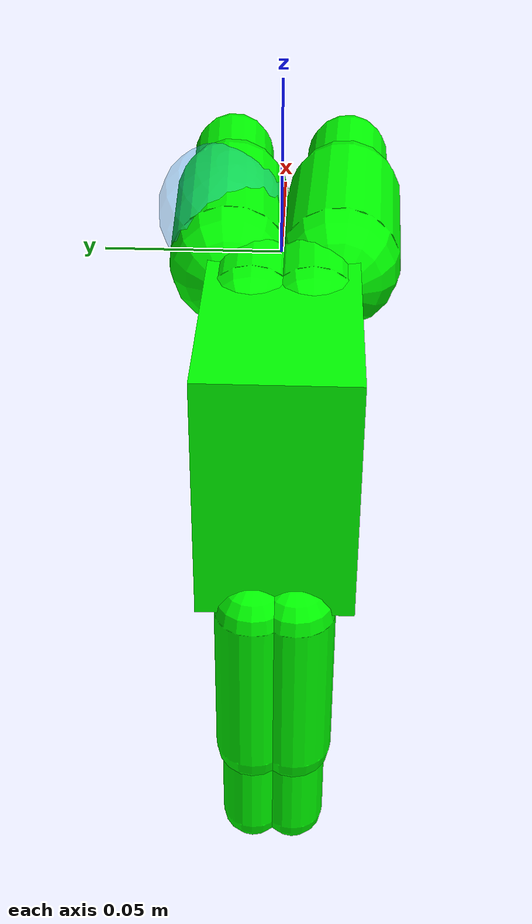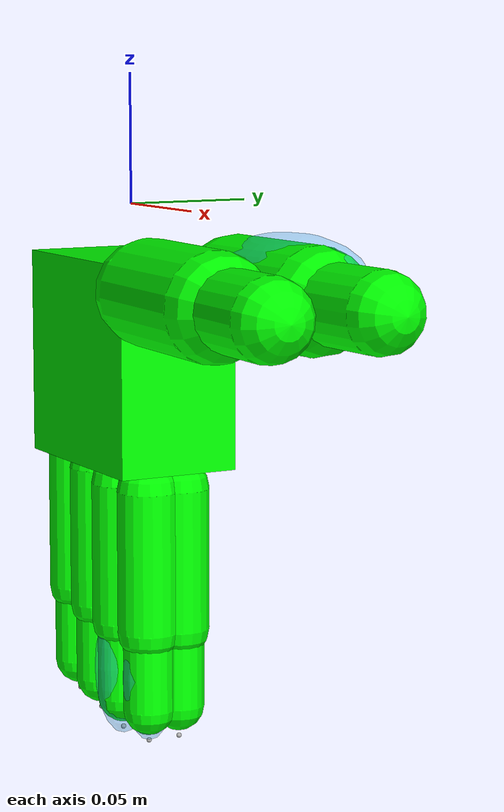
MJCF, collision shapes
<mujoco model="taco_pour_bowl_plate_20230927_017">
  <compiler angle="radian" meshdir="/data_all/zzx/3.2RL/models/taco_xhand/assets" />
  <option sdf_iterations="10" sdf_initpoints="40" />
  <default>
    <joint armature="1" />
    <geom contype="0" conaffinity="0" condim="1" density="800" />
    <site group="3" rgba="1 0 0 1" />
    <general biastype="affine" gainprm="300" biasprm="0 -300 1" />
  </default>
  <asset>
    <texture type="skybox" colorspace="auto" builtin="gradient" rgb1="1 1 1" rgb2="1 1 1" width="512" height="3072" />
    <texture type="2d" colorspace="auto" name="right_groundplane" builtin="checker" mark="edge" rgb1="0.2 0.3 0.4" rgb2="0.1 0.2 0.3" markrgb="0.8 0.8 0.8" width="300" height="300" />
    <texture type="skybox" colorspace="auto" builtin="gradient" rgb1="0.3 0.5 0.7" rgb2="0 0 0" width="512" height="3072" />
    <texture type="2d" colorspace="auto" name="left_groundplane" builtin="checker" mark="edge" rgb1="0.2 0.3 0.4" rgb2="0.1 0.2 0.3" markrgb="0.8 0.8 0.8" width="300" height="300" />
    <texture type="cube" colorspace="auto" name="skybox" builtin="gradient" rgb1="0.3 0.5 0.7" rgb2="0 0 0" width="512" height="3072" />
    <texture type="cube" colorspace="auto" name="groundplane" builtin="checker" mark="edge" rgb1="0.2 0.3 0.4" rgb2="0.1 0.2 0.3" markrgb="0.8 0.8 0.8" width="300" height="1800" />
    <material name="right_groundplane" texture="right_groundplane" texuniform="true" texrepeat="5 5" reflectance="0.2" />
    <material name="left_groundplane" texture="left_groundplane" texuniform="true" texrepeat="5 5" reflectance="0.2" />
    <material name="groundplane" texuniform="true" texrepeat="5 5" reflectance="0.2" />
    <mesh name="right_hand_link" content_type="model/stl" file="robots/xhand_pour_20230927_017/assets/right_hand_link.STL" />
    <mesh name="right_hand_thumb_bend_link" content_type="model/stl" file="robots/xhand_pour_20230927_017/assets/right_hand_thumb_bend_link.STL" />
    <mesh name="right_hand_thumb_rota_link1" content_type="model/stl" file="robots/xhand_pour_20230927_017/assets/right_hand_thumb_rota_link1.STL" />
    <mesh name="right_hand_thumb_rota_link2" content_type="model/stl" file="robots/xhand_pour_20230927_017/assets/right_hand_thumb_rota_link2.STL" />
    <mesh name="right_hand_index_bend_link" content_type="model/stl" file="robots/xhand_pour_20230927_017/assets/right_hand_index_bend_link.STL" />
    <mesh name="right_hand_index_rota_link1" content_type="model/stl" file="robots/xhand_pour_20230927_017/assets/right_hand_index_rota_link1.STL" />
    <mesh name="right_hand_index_rota_link2" content_type="model/stl" file="robots/xhand_pour_20230927_017/assets/right_hand_index_rota_link2.STL" />
    <mesh name="right_hand_mid_link1" content_type="model/stl" file="robots/xhand_pour_20230927_017/assets/right_hand_mid_link1.STL" />
    <mesh name="right_hand_mid_link2" content_type="model/stl" file="robots/xhand_pour_20230927_017/assets/right_hand_mid_link2.STL" />
    <mesh name="right_hand_ring_link1" content_type="model/stl" file="robots/xhand_pour_20230927_017/assets/right_hand_ring_link1.STL" />
    <mesh name="right_hand_ring_link2" content_type="model/stl" file="robots/xhand_pour_20230927_017/assets/right_hand_ring_link2.STL" />
    <mesh name="right_hand_pinky_link1" content_type="model/stl" file="robots/xhand_pour_20230927_017/assets/right_hand_pinky_link1.STL" />
    <mesh name="right_hand_pinky_link2" content_type="model/stl" file="robots/xhand_pour_20230927_017/assets/right_hand_pinky_link2.STL" />
    <mesh name="left_hand_link" content_type="model/stl" file="robots/xhand_pour_20230927_017/assets/left_hand_link.STL" />
    <mesh name="left_hand_thumb_bend_link" content_type="model/stl" file="robots/xhand_pour_20230927_017/assets/left_hand_thumb_bend_link.STL" />
    <mesh name="left_hand_thumb_rota_link1" content_type="model/stl" file="robots/xhand_pour_20230927_017/assets/left_hand_thumb_rota_link1.STL" />
    <mesh name="left_hand_thumb_rota_link2" content_type="model/stl" file="robots/xhand_pour_20230927_017/assets/left_hand_thumb_rota_link2.STL" />
    <mesh name="left_hand_index_bend_link" content_type="model/stl" file="robots/xhand_pour_20230927_017/assets/left_hand_index_bend_link.STL" />
    <mesh name="left_hand_index_rota_link1" content_type="model/stl" file="robots/xhand_pour_20230927_017/assets/left_hand_index_rota_link1.STL" />
    <mesh name="left_hand_index_rota_link2" content_type="model/stl" file="robots/xhand_pour_20230927_017/assets/left_hand_index_rota_link2.STL" />
    <mesh name="left_hand_mid_link1" content_type="model/stl" file="robots/xhand_pour_20230927_017/assets/left_hand_mid_link1.STL" />
    <mesh name="left_hand_mid_link2" content_type="model/stl" file="robots/xhand_pour_20230927_017/assets/left_hand_mid_link2.STL" />
    <mesh name="left_hand_ring_link1" content_type="model/stl" file="robots/xhand_pour_20230927_017/assets/left_hand_ring_link1.STL" />
    <mesh name="left_hand_ring_link2" content_type="model/stl" file="robots/xhand_pour_20230927_017/assets/left_hand_ring_link2.STL" />
    <mesh name="left_hand_pinky_link1" content_type="model/stl" file="robots/xhand_pour_20230927_017/assets/left_hand_pinky_link1.STL" />
    <mesh name="left_hand_pinky_link2" content_type="model/stl" file="robots/xhand_pour_20230927_017/assets/left_hand_pinky_link2.STL" />
    <mesh name="right_visual" file="objects/022/visual.obj" scale="0.01 0.01 0.01" />
    <mesh name="right_0" file="objects/022/convex_m/0.obj" />
    <mesh name="right_1" file="objects/022/convex_m/1.obj" />
    <mesh name="right_2" file="objects/022/convex_m/2.obj" />
    <mesh name="right_3" file="objects/022/convex_m/3.obj" />
    <mesh name="right_4" file="objects/022/convex_m/4.obj" />
    <mesh name="right_5" file="objects/022/convex_m/5.obj" />
    <mesh name="right_6" file="objects/022/convex_m/6.obj" />
    <mesh name="right_7" file="objects/022/convex_m/7.obj" />
    <mesh name="right_8" file="objects/022/convex_m/8.obj" />
    <mesh name="right_9" file="objects/022/convex_m/9.obj" />
    <mesh name="right_10" file="objects/022/convex_m/10.obj" />
    <mesh name="right_11" file="objects/022/convex_m/11.obj" />
    <mesh name="right_12" file="objects/022/convex_m/12.obj" />
    <mesh name="right_13" file="objects/022/convex_m/13.obj" />
    <mesh name="right_14" file="objects/022/convex_m/14.obj" />
    <mesh name="right_15" file="objects/022/convex_m/15.obj" />
    <mesh name="right_16" file="objects/022/convex_m/16.obj" />
    <mesh name="right_17" file="objects/022/convex_m/17.obj" />
    <mesh name="right_18" file="objects/022/convex_m/18.obj" />
    <mesh name="right_19" file="objects/022/convex_m/19.obj" />
    <mesh name="right_20" file="objects/022/convex_m/20.obj" />
    <mesh name="right_21" file="objects/022/convex_m/21.obj" />
    <mesh name="right_22" file="objects/022/convex_m/22.obj" />
    <mesh name="right_23" file="objects/022/convex_m/23.obj" />
    <mesh name="right_24" file="objects/022/convex_m/24.obj" />
    <mesh name="right_25" file="objects/022/convex_m/25.obj" />
    <mesh name="right_26" file="objects/022/convex_m/26.obj" />
    <mesh name="right_27" file="objects/022/convex_m/27.obj" />
    <mesh name="right_28" file="objects/022/convex_m/28.obj" />
    <mesh name="right_29" file="objects/022/convex_m/29.obj" />
    <mesh name="right_30" file="objects/022/convex_m/30.obj" />
    <mesh name="right_31" file="objects/022/convex_m/31.obj" />
    <mesh name="left_visual" file="objects/135/visual.obj" scale="0.01 0.01 0.01" />
    <mesh name="left_0" file="objects/135/convex_m/0.obj" />
    <mesh name="left_1" file="objects/135/convex_m/1.obj" />
    <mesh name="left_2" file="objects/135/convex_m/2.obj" />
    <mesh name="left_3" file="objects/135/convex_m/3.obj" />
    <mesh name="left_4" file="objects/135/convex_m/4.obj" />
    <mesh name="left_5" file="objects/135/convex_m/5.obj" />
    <mesh name="left_6" file="objects/135/convex_m/6.obj" />
    <mesh name="left_7" file="objects/135/convex_m/7.obj" />
    <mesh name="left_8" file="objects/135/convex_m/8.obj" />
    <mesh name="left_9" file="objects/135/convex_m/9.obj" />
    <mesh name="left_10" file="objects/135/convex_m/10.obj" />
    <mesh name="left_11" file="objects/135/convex_m/11.obj" />
    <mesh name="left_12" file="objects/135/convex_m/12.obj" />
    <mesh name="left_13" file="objects/135/convex_m/13.obj" />
    <mesh name="left_14" file="objects/135/convex_m/14.obj" />
    <mesh name="left_15" file="objects/135/convex_m/15.obj" />
    <mesh name="left_16" file="objects/135/convex_m/16.obj" />
    <mesh name="left_17" file="objects/135/convex_m/17.obj" />
    <mesh name="left_18" file="objects/135/convex_m/18.obj" />
    <mesh name="left_19" file="objects/135/convex_m/19.obj" />
    <mesh name="left_20" file="objects/135/convex_m/20.obj" />
    <mesh name="left_21" file="objects/135/convex_m/21.obj" />
    <mesh name="left_22" file="objects/135/convex_m/22.obj" />
    <mesh name="left_23" file="objects/135/convex_m/23.obj" />
    <mesh name="left_24" file="objects/135/convex_m/24.obj" />
    <mesh name="left_25" file="objects/135/convex_m/25.obj" />
    <mesh name="left_26" file="objects/135/convex_m/26.obj" />
    <mesh name="left_27" file="objects/135/convex_m/27.obj" />
    <mesh name="left_28" file="objects/135/convex_m/28.obj" />
    <mesh name="left_29" file="objects/135/convex_m/29.obj" />
    <mesh name="left_30" file="objects/135/convex_m/30.obj" />
    <mesh name="left_31" file="objects/135/convex_m/31.obj" />
    <mesh name="left_palm_thumb_guard_palm_mesh_08167" file="../../../runs/taco_pour_left_palm_thumb_local_surface_guard_v1/assets/palm/face_08167.obj" />
    <mesh name="left_palm_thumb_guard_palm_mesh_08168" file="../../../runs/taco_pour_left_palm_thumb_local_surface_guard_v1/assets/palm/face_08168.obj" />
    <mesh name="left_palm_thumb_guard_palm_mesh_08179" file="../../../runs/taco_pour_left_palm_thumb_local_surface_guard_v1/assets/palm/face_08179.obj" />
    <mesh name="left_palm_thumb_guard_palm_mesh_08180" file="../../../runs/taco_pour_left_palm_thumb_local_surface_guard_v1/assets/palm/face_08180.obj" />
    <mesh name="left_palm_thumb_guard_palm_mesh_08195" file="../../../runs/taco_pour_left_palm_thumb_local_surface_guard_v1/assets/palm/face_08195.obj" />
    <mesh name="left_palm_thumb_guard_palm_mesh_08207" file="../../../runs/taco_pour_left_palm_thumb_local_surface_guard_v1/assets/palm/face_08207.obj" />
    <mesh name="left_palm_thumb_guard_palm_mesh_08208" file="../../../runs/taco_pour_left_palm_thumb_local_surface_guard_v1/assets/palm/face_08208.obj" />
    <mesh name="left_palm_thumb_guard_palm_mesh_08223" file="../../../runs/taco_pour_left_palm_thumb_local_surface_guard_v1/assets/palm/face_08223.obj" />
    <mesh name="left_palm_thumb_guard_palm_mesh_08224" file="../../../runs/taco_pour_left_palm_thumb_local_surface_guard_v1/assets/palm/face_08224.obj" />
    <mesh name="left_palm_thumb_guard_palm_mesh_11726" file="../../../runs/taco_pour_left_palm_thumb_local_surface_guard_v1/assets/palm/face_11726.obj" />
    <mesh name="left_palm_thumb_guard_palm_mesh_11747" file="../../../runs/taco_pour_left_palm_thumb_local_surface_guard_v1/assets/palm/face_11747.obj" />
    <mesh name="left_palm_thumb_guard_palm_mesh_11748" file="../../../runs/taco_pour_left_palm_thumb_local_surface_guard_v1/assets/palm/face_11748.obj" />
    <mesh name="left_palm_thumb_guard_palm_mesh_11749" file="../../../runs/taco_pour_left_palm_thumb_local_surface_guard_v1/assets/palm/face_11749.obj" />
    <mesh name="left_palm_thumb_guard_palm_mesh_11776" file="../../../runs/taco_pour_left_palm_thumb_local_surface_guard_v1/assets/palm/face_11776.obj" />
    <mesh name="left_palm_thumb_guard_palm_mesh_11779" file="../../../runs/taco_pour_left_palm_thumb_local_surface_guard_v1/assets/palm/face_11779.obj" />
    <mesh name="left_palm_thumb_guard_palm_mesh_11780" file="../../../runs/taco_pour_left_palm_thumb_local_surface_guard_v1/assets/palm/face_11780.obj" />
    <mesh name="left_palm_thumb_guard_palm_mesh_11781" file="../../../runs/taco_pour_left_palm_thumb_local_surface_guard_v1/assets/palm/face_11781.obj" />
    <mesh name="left_palm_thumb_guard_palm_mesh_11782" file="../../../runs/taco_pour_left_palm_thumb_local_surface_guard_v1/assets/palm/face_11782.obj" />
    <mesh name="left_palm_thumb_guard_palm_mesh_11783" file="../../../runs/taco_pour_left_palm_thumb_local_surface_guard_v1/assets/palm/face_11783.obj" />
    <mesh name="left_palm_thumb_guard_palm_mesh_11789" file="../../../runs/taco_pour_left_palm_thumb_local_surface_guard_v1/assets/palm/face_11789.obj" />
    <mesh name="left_palm_thumb_guard_palm_mesh_11790" file="../../../runs/taco_pour_left_palm_thumb_local_surface_guard_v1/assets/palm/face_11790.obj" />
    <mesh name="left_palm_thumb_guard_palm_mesh_11791" file="../../../runs/taco_pour_left_palm_thumb_local_surface_guard_v1/assets/palm/face_11791.obj" />
    <mesh name="left_palm_thumb_guard_palm_mesh_11792" file="../../../runs/taco_pour_left_palm_thumb_local_surface_guard_v1/assets/palm/face_11792.obj" />
    <mesh name="left_palm_thumb_guard_palm_mesh_11793" file="../../../runs/taco_pour_left_palm_thumb_local_surface_guard_v1/assets/palm/face_11793.obj" />
    <mesh name="left_palm_thumb_guard_palm_mesh_11819" file="../../../runs/taco_pour_left_palm_thumb_local_surface_guard_v1/assets/palm/face_11819.obj" />
    <mesh name="left_palm_thumb_guard_palm_mesh_11830" file="../../../runs/taco_pour_left_palm_thumb_local_surface_guard_v1/assets/palm/face_11830.obj" />
    <mesh name="left_palm_thumb_guard_palm_mesh_11854" file="../../../runs/taco_pour_left_palm_thumb_local_surface_guard_v1/assets/palm/face_11854.obj" />
    <mesh name="left_palm_thumb_guard_palm_mesh_11855" file="../../../runs/taco_pour_left_palm_thumb_local_surface_guard_v1/assets/palm/face_11855.obj" />
    <mesh name="left_palm_thumb_guard_palm_mesh_15597" file="../../../runs/taco_pour_left_palm_thumb_local_surface_guard_v1/assets/palm/face_15597.obj" />
    <mesh name="left_palm_thumb_guard_palm_mesh_15598" file="../../../runs/taco_pour_left_palm_thumb_local_surface_guard_v1/assets/palm/face_15598.obj" />
    <mesh name="left_palm_thumb_guard_palm_mesh_15599" file="../../../runs/taco_pour_left_palm_thumb_local_surface_guard_v1/assets/palm/face_15599.obj" />
    <mesh name="left_palm_thumb_guard_palm_mesh_15600" file="../../../runs/taco_pour_left_palm_thumb_local_surface_guard_v1/assets/palm/face_15600.obj" />
    <mesh name="left_palm_thumb_guard_palm_mesh_15601" file="../../../runs/taco_pour_left_palm_thumb_local_surface_guard_v1/assets/palm/face_15601.obj" />
    <mesh name="left_palm_thumb_guard_palm_mesh_15602" file="../../../runs/taco_pour_left_palm_thumb_local_surface_guard_v1/assets/palm/face_15602.obj" />
    <mesh name="left_palm_thumb_guard_palm_mesh_15603" file="../../../runs/taco_pour_left_palm_thumb_local_surface_guard_v1/assets/palm/face_15603.obj" />
    <mesh name="left_palm_thumb_guard_palm_mesh_15604" file="../../../runs/taco_pour_left_palm_thumb_local_surface_guard_v1/assets/palm/face_15604.obj" />
    <mesh name="left_palm_thumb_guard_palm_mesh_15605" file="../../../runs/taco_pour_left_palm_thumb_local_surface_guard_v1/assets/palm/face_15605.obj" />
    <mesh name="left_palm_thumb_guard_palm_mesh_15606" file="../../../runs/taco_pour_left_palm_thumb_local_surface_guard_v1/assets/palm/face_15606.obj" />
    <mesh name="left_palm_thumb_guard_palm_mesh_15607" file="../../../runs/taco_pour_left_palm_thumb_local_surface_guard_v1/assets/palm/face_15607.obj" />
    <mesh name="left_palm_thumb_guard_palm_mesh_15613" file="../../../runs/taco_pour_left_palm_thumb_local_surface_guard_v1/assets/palm/face_15613.obj" />
    <mesh name="left_palm_thumb_guard_palm_mesh_15614" file="../../../runs/taco_pour_left_palm_thumb_local_surface_guard_v1/assets/palm/face_15614.obj" />
    <mesh name="left_palm_thumb_guard_palm_mesh_15615" file="../../../runs/taco_pour_left_palm_thumb_local_surface_guard_v1/assets/palm/face_15615.obj" />
    <mesh name="left_palm_thumb_guard_palm_mesh_15625" file="../../../runs/taco_pour_left_palm_thumb_local_surface_guard_v1/assets/palm/face_15625.obj" />
    <mesh name="left_palm_thumb_guard_palm_mesh_15639" file="../../../runs/taco_pour_left_palm_thumb_local_surface_guard_v1/assets/palm/face_15639.obj" />
    <mesh name="left_palm_thumb_guard_palm_mesh_15640" file="../../../runs/taco_pour_left_palm_thumb_local_surface_guard_v1/assets/palm/face_15640.obj" />
    <mesh name="left_palm_thumb_guard_thumb_mesh_10971" file="../../../runs/taco_pour_left_palm_thumb_local_surface_guard_v1/assets/thumb/face_10971.obj" />
    <mesh name="left_palm_thumb_guard_thumb_mesh_10980" file="../../../runs/taco_pour_left_palm_thumb_local_surface_guard_v1/assets/thumb/face_10980.obj" />
    <mesh name="left_palm_thumb_guard_thumb_mesh_10981" file="../../../runs/taco_pour_left_palm_thumb_local_surface_guard_v1/assets/thumb/face_10981.obj" />
    <mesh name="left_palm_thumb_guard_thumb_mesh_10982" file="../../../runs/taco_pour_left_palm_thumb_local_surface_guard_v1/assets/thumb/face_10982.obj" />
    <mesh name="left_palm_thumb_guard_thumb_mesh_10983" file="../../../runs/taco_pour_left_palm_thumb_local_surface_guard_v1/assets/thumb/face_10983.obj" />
    <mesh name="left_palm_thumb_guard_thumb_mesh_10985" file="../../../runs/taco_pour_left_palm_thumb_local_surface_guard_v1/assets/thumb/face_10985.obj" />
    <mesh name="left_palm_thumb_guard_thumb_mesh_10986" file="../../../runs/taco_pour_left_palm_thumb_local_surface_guard_v1/assets/thumb/face_10986.obj" />
    <mesh name="left_palm_thumb_guard_thumb_mesh_10987" file="../../../runs/taco_pour_left_palm_thumb_local_surface_guard_v1/assets/thumb/face_10987.obj" />
    <mesh name="left_palm_thumb_guard_thumb_mesh_10988" file="../../../runs/taco_pour_left_palm_thumb_local_surface_guard_v1/assets/thumb/face_10988.obj" />
    <mesh name="left_palm_thumb_guard_thumb_mesh_10989" file="../../../runs/taco_pour_left_palm_thumb_local_surface_guard_v1/assets/thumb/face_10989.obj" />
    <mesh name="left_palm_thumb_guard_thumb_mesh_10990" file="../../../runs/taco_pour_left_palm_thumb_local_surface_guard_v1/assets/thumb/face_10990.obj" />
    <mesh name="left_palm_thumb_guard_thumb_mesh_10991" file="../../../runs/taco_pour_left_palm_thumb_local_surface_guard_v1/assets/thumb/face_10991.obj" />
    <mesh name="left_palm_thumb_guard_thumb_mesh_10992" file="../../../runs/taco_pour_left_palm_thumb_local_surface_guard_v1/assets/thumb/face_10992.obj" />
    <mesh name="left_palm_thumb_guard_thumb_mesh_10993" file="../../../runs/taco_pour_left_palm_thumb_local_surface_guard_v1/assets/thumb/face_10993.obj" />
    <mesh name="left_palm_thumb_guard_thumb_mesh_10994" file="../../../runs/taco_pour_left_palm_thumb_local_surface_guard_v1/assets/thumb/face_10994.obj" />
    <mesh name="left_palm_thumb_guard_thumb_mesh_10995" file="../../../runs/taco_pour_left_palm_thumb_local_surface_guard_v1/assets/thumb/face_10995.obj" />
    <mesh name="left_palm_thumb_guard_thumb_mesh_10996" file="../../../runs/taco_pour_left_palm_thumb_local_surface_guard_v1/assets/thumb/face_10996.obj" />
    <mesh name="left_palm_thumb_guard_thumb_mesh_11007" file="../../../runs/taco_pour_left_palm_thumb_local_surface_guard_v1/assets/thumb/face_11007.obj" />
    <mesh name="left_palm_thumb_guard_thumb_mesh_11008" file="../../../runs/taco_pour_left_palm_thumb_local_surface_guard_v1/assets/thumb/face_11008.obj" />
    <mesh name="left_palm_thumb_guard_thumb_mesh_11009" file="../../../runs/taco_pour_left_palm_thumb_local_surface_guard_v1/assets/thumb/face_11009.obj" />
    <mesh name="left_palm_thumb_guard_thumb_mesh_11011" file="../../../runs/taco_pour_left_palm_thumb_local_surface_guard_v1/assets/thumb/face_11011.obj" />
    <mesh name="left_palm_thumb_guard_thumb_mesh_11012" file="../../../runs/taco_pour_left_palm_thumb_local_surface_guard_v1/assets/thumb/face_11012.obj" />
    <mesh name="left_palm_thumb_guard_thumb_mesh_11013" file="../../../runs/taco_pour_left_palm_thumb_local_surface_guard_v1/assets/thumb/face_11013.obj" />
    <mesh name="left_palm_thumb_guard_thumb_mesh_11219" file="../../../runs/taco_pour_left_palm_thumb_local_surface_guard_v1/assets/thumb/face_11219.obj" />
    <mesh name="left_palm_thumb_guard_thumb_mesh_11220" file="../../../runs/taco_pour_left_palm_thumb_local_surface_guard_v1/assets/thumb/face_11220.obj" />
    <mesh name="left_palm_thumb_guard_thumb_mesh_11221" file="../../../runs/taco_pour_left_palm_thumb_local_surface_guard_v1/assets/thumb/face_11221.obj" />
    <mesh name="left_palm_thumb_guard_thumb_mesh_11222" file="../../../runs/taco_pour_left_palm_thumb_local_surface_guard_v1/assets/thumb/face_11222.obj" />
    <mesh name="left_palm_thumb_guard_thumb_mesh_11223" file="../../../runs/taco_pour_left_palm_thumb_local_surface_guard_v1/assets/thumb/face_11223.obj" />
    <mesh name="left_palm_thumb_guard_thumb_mesh_11227" file="../../../runs/taco_pour_left_palm_thumb_local_surface_guard_v1/assets/thumb/face_11227.obj" />
    <mesh name="left_palm_thumb_guard_thumb_mesh_11228" file="../../../runs/taco_pour_left_palm_thumb_local_surface_guard_v1/assets/thumb/face_11228.obj" />
    <mesh name="left_palm_thumb_guard_thumb_mesh_11229" file="../../../runs/taco_pour_left_palm_thumb_local_surface_guard_v1/assets/thumb/face_11229.obj" />
    <mesh name="left_palm_thumb_guard_thumb_mesh_11230" file="../../../runs/taco_pour_left_palm_thumb_local_surface_guard_v1/assets/thumb/face_11230.obj" />
    <mesh name="left_palm_thumb_guard_thumb_mesh_11231" file="../../../runs/taco_pour_left_palm_thumb_local_surface_guard_v1/assets/thumb/face_11231.obj" />
    <mesh name="left_palm_thumb_guard_thumb_mesh_11232" file="../../../runs/taco_pour_left_palm_thumb_local_surface_guard_v1/assets/thumb/face_11232.obj" />
    <mesh name="left_palm_thumb_guard_thumb_mesh_11244" file="../../../runs/taco_pour_left_palm_thumb_local_surface_guard_v1/assets/thumb/face_11244.obj" />
    <mesh name="left_palm_thumb_guard_thumb_mesh_11245" file="../../../runs/taco_pour_left_palm_thumb_local_surface_guard_v1/assets/thumb/face_11245.obj" />
    <mesh name="left_palm_thumb_guard_thumb_mesh_11246" file="../../../runs/taco_pour_left_palm_thumb_local_surface_guard_v1/assets/thumb/face_11246.obj" />
    <mesh name="left_palm_thumb_guard_thumb_mesh_11286" file="../../../runs/taco_pour_left_palm_thumb_local_surface_guard_v1/assets/thumb/face_11286.obj" />
    <mesh name="left_palm_thumb_guard_thumb_mesh_11287" file="../../../runs/taco_pour_left_palm_thumb_local_surface_guard_v1/assets/thumb/face_11287.obj" />
    <mesh name="left_palm_thumb_guard_thumb_mesh_11288" file="../../../runs/taco_pour_left_palm_thumb_local_surface_guard_v1/assets/thumb/face_11288.obj" />
    <mesh name="left_palm_thumb_guard_thumb_mesh_11289" file="../../../runs/taco_pour_left_palm_thumb_local_surface_guard_v1/assets/thumb/face_11289.obj" />
    <mesh name="left_palm_thumb_guard_thumb_mesh_11290" file="../../../runs/taco_pour_left_palm_thumb_local_surface_guard_v1/assets/thumb/face_11290.obj" />
    <mesh name="left_palm_thumb_guard_thumb_mesh_11291" file="../../../runs/taco_pour_left_palm_thumb_local_surface_guard_v1/assets/thumb/face_11291.obj" />
    <mesh name="left_palm_thumb_guard_thumb_mesh_11292" file="../../../runs/taco_pour_left_palm_thumb_local_surface_guard_v1/assets/thumb/face_11292.obj" />
    <mesh name="left_palm_thumb_guard_thumb_mesh_11293" file="../../../runs/taco_pour_left_palm_thumb_local_surface_guard_v1/assets/thumb/face_11293.obj" />
    <mesh name="left_palm_thumb_guard_thumb_mesh_11294" file="../../../runs/taco_pour_left_palm_thumb_local_surface_guard_v1/assets/thumb/face_11294.obj" />
    <mesh name="left_palm_thumb_guard_thumb_mesh_11295" file="../../../runs/taco_pour_left_palm_thumb_local_surface_guard_v1/assets/thumb/face_11295.obj" />
    <mesh name="left_palm_thumb_guard_thumb_mesh_11296" file="../../../runs/taco_pour_left_palm_thumb_local_surface_guard_v1/assets/thumb/face_11296.obj" />
    <mesh name="left_palm_thumb_guard_thumb_mesh_11297" file="../../../runs/taco_pour_left_palm_thumb_local_surface_guard_v1/assets/thumb/face_11297.obj" />
    <mesh name="left_palm_thumb_guard_thumb_mesh_11306" file="../../../runs/taco_pour_left_palm_thumb_local_surface_guard_v1/assets/thumb/face_11306.obj" />
    <mesh name="left_palm_thumb_guard_thumb_mesh_11307" file="../../../runs/taco_pour_left_palm_thumb_local_surface_guard_v1/assets/thumb/face_11307.obj" />
    <mesh name="left_palm_thumb_guard_thumb_mesh_11308" file="../../../runs/taco_pour_left_palm_thumb_local_surface_guard_v1/assets/thumb/face_11308.obj" />
    <mesh name="left_palm_thumb_guard_thumb_mesh_11309" file="../../../runs/taco_pour_left_palm_thumb_local_surface_guard_v1/assets/thumb/face_11309.obj" />
    <mesh name="left_palm_thumb_guard_thumb_mesh_11310" file="../../../runs/taco_pour_left_palm_thumb_local_surface_guard_v1/assets/thumb/face_11310.obj" />
    <mesh name="left_palm_thumb_guard_thumb_mesh_11311" file="../../../runs/taco_pour_left_palm_thumb_local_surface_guard_v1/assets/thumb/face_11311.obj" />
    <mesh name="left_palm_thumb_guard_thumb_mesh_11312" file="../../../runs/taco_pour_left_palm_thumb_local_surface_guard_v1/assets/thumb/face_11312.obj" />
    <mesh name="left_palm_thumb_guard_thumb_mesh_11313" file="../../../runs/taco_pour_left_palm_thumb_local_surface_guard_v1/assets/thumb/face_11313.obj" />
    <mesh name="left_palm_thumb_guard_thumb_mesh_11314" file="../../../runs/taco_pour_left_palm_thumb_local_surface_guard_v1/assets/thumb/face_11314.obj" />
    <mesh name="left_palm_thumb_guard_thumb_mesh_11315" file="../../../runs/taco_pour_left_palm_thumb_local_surface_guard_v1/assets/thumb/face_11315.obj" />
    <mesh name="left_palm_thumb_guard_thumb_mesh_11316" file="../../../runs/taco_pour_left_palm_thumb_local_surface_guard_v1/assets/thumb/face_11316.obj" />
    <mesh name="left_palm_thumb_guard_thumb_mesh_11317" file="../../../runs/taco_pour_left_palm_thumb_local_surface_guard_v1/assets/thumb/face_11317.obj" />
    <mesh name="left_palm_thumb_guard_thumb_mesh_11318" file="../../../runs/taco_pour_left_palm_thumb_local_surface_guard_v1/assets/thumb/face_11318.obj" />
  </asset>
  <worldbody>
    <geom name="floor" size="0 0 0.05" type="plane" material="right_groundplane" contype="0" conaffinity="0" condim="3" friction="1 0.1 0" pos="0 0 0.72" />
    <camera name="front" pos="0.031 0.941 0.844" quat="0.0150738 0.00673439 0.407848 0.912901" mode="fixed" />
    <body name="R_forearm_ty_link">
      <inertial pos="0 0 0" mass="0.1" diaginertia="0.01 0.01 0.01" />
      <joint name="R_forearm_tx_link_joint" pos="0 0 0" axis="1 0 0" type="slide" range="-5 5" />
      <body name="R_forearm_tz_link">
        <inertial pos="0 0 0" mass="0.1" diaginertia="0.01 0.01 0.01" />
        <joint name="R_forearm_ty_link_joint" pos="0 0 0" axis="0 1 0" type="slide" range="-5 5" />
        <body name="R_forearm_roll_link">
          <inertial pos="0 0 0" mass="0.1" diaginertia="0.01 0.01 0.01" />
          <joint name="R_forearm_tz_link_joint" pos="0 0 0" axis="0 0 1" type="slide" range="-5 5" />
          <body name="R_forearm_pitch_link">
            <inertial pos="0 0 0" mass="0.1" diaginertia="0.01 0.01 0.01" />
            <joint name="R_forearm_roll_link_joint" pos="0 0 0" axis="0 0 1" range="-6.2 6.2" />
            <body name="R_forearm_yaw_link">
              <inertial pos="0 0 0" mass="0.1" diaginertia="0.01 0.01 0.01" />
              <joint name="R_forearm_pitch_link_joint" pos="0 0 0" axis="1 0 0" range="-6.2 6.2" />
              <body name="right_hand_link">
                <inertial pos="-0.0071397 0.00342244 -0.0584807" quat="0.688453 0.098553 0.0886255 0.713068" mass="0.530025" diaginertia="0.00067782 0.000491189 0.000335821" />
                <joint name="R_forearm_yaw_link_joint" pos="0 0 0" axis="0 -1 0" range="-6.2 6.2" />
                <geom name="right_hand_link_visual" type="mesh" group="1" density="0" rgba="0.792157 0.819608 0.933333 1" mesh="right_hand_link" contype="0" conaffinity="0" />
                <geom name="collision_hand_right_palm_0" size="0.04 0.024 0.04" pos="0 0 -0.06" type="box" group="3" rgba="0 1 0 1" contype="0" conaffinity="0" condim="3" friction="1 0.1 0" />
                <geom name="collision_hand_right_palm_index_root_negative_guard" size="0.000929064511788" pos="0.0133624176979 0.00650000011921 -0.0615201568604" type="sphere" group="3" density="0" rgba="1 0.75 0 1" contype="0" conaffinity="0" condim="3" friction="1 0.1 0" />
                <geom name="collision_hand_right_palm_index_root_positive_guard" size="0.00150030451896" pos="0.0374132442474 -0.0005 -0.0731002693176" type="sphere" group="3" density="0" rgba="1 0.75 0 1" contype="0" conaffinity="0" condim="3" friction="1 0.1 0" />
                <site name="right_palm" pos="0 0 0" quat="0 0.707107 0.707107 0" size="0.01 0.02 0.03" type="box" />
                <body name="right_hand_thumb_bend_link" pos="0.0228 0.0095 -0.0305">
                  <inertial pos="0.0145291 -0.000901303 -0.000127926" quat="0.0288921 0.68936 0.0166971 0.72365" mass="0.00985529" diaginertia="1.30647e-06 1.29142e-06 5.40953e-07" />
                  <joint name="right_hand_thumb_bend_joint" pos="0 0 0" axis="0 0 1" range="0 1.83" />
                  <geom name="right_thumb_bend_visual" type="mesh" group="1" density="0" rgba="0.890196 0.890196 0.913725 1" mesh="right_hand_thumb_bend_link" contype="0" conaffinity="0" />
                  <geom name="collision_hand_right_thumb_2" size="0.015 0.01" pos="0.01 0 0" quat="0.707107 0 -0.707107 0" type="capsule" group="3" rgba="0 1 0 1" contype="0" conaffinity="0" condim="3" friction="1 0.1 0" />
                  <body name="right_hand_thumb_rota_link1" pos="0.028599 0.0083177 0.00178" quat="0.99124 0.130499 0.00265603 0.0201745">
                    <inertial pos="0.0279237 -0.000127603 -0.000272577" quat="-0.0989965 0.703671 0.0850598 0.698435" mass="0.153265" diaginertia="5.62327e-05 4.89801e-05 2.23924e-05" />
                    <joint name="right_hand_thumb_rota_joint1" pos="0 0 0" axis="0 1 0" range="-1.05 1.57" />
                    <geom name="right_thumb_rota1_visual" type="mesh" group="1" density="0" rgba="1 1 1 1" mesh="right_hand_thumb_rota_link1" contype="0" conaffinity="0" />
                    <geom name="collision_hand_right_thumb_1" size="0.02 0.0275" pos="0.0275 0 0" quat="0.707107 0 -0.707107 0" type="capsule" group="3" rgba="0 1 0 1" contype="0" conaffinity="0" condim="3" friction="1 0.1 0" />
                    <body name="right_hand_thumb_rota_link2" pos="0.0553 0 0">
                      <inertial pos="0.0224697 -0.000691342 0.00302232" quat="-0.0604029 0.715612 0.0198067 0.695599" mass="0.0374004" diaginertia="9.5465e-06 8.27017e-06 3.92137e-06" />
                      <joint name="right_hand_thumb_rota_joint2" pos="0 0 0" axis="0 1 0" range="-0.175 1.83" />
                      <geom name="right_thumb_rota2_visual" type="mesh" group="1" density="0" rgba="0.792157 0.819608 0.933333 1" mesh="right_hand_thumb_rota_link2" contype="0" conaffinity="0" />
                      <geom name="collision_hand_right_thumb_0" size="0.015 0.02" pos="0.02 0 0" quat="0.707107 0 -0.707107 0" type="capsule" group="3" rgba="0 1 0 1" contype="0" conaffinity="0" condim="3" friction="1 0.1 0" />
                      <geom size="0.001" pos="0.0504025 0 0" group="1" density="0" rgba="0.698039 0.698039 0.698039 1" contype="0" conaffinity="0" />
                      <site name="right_thumb_tip" pos="0.04 0 -0.012" />
                      <site name="track_hand_right_thumb_tip" pos="0.04 0 -0.012" />
                      <site name="trace_hand_right_thumb_tip" pos="0.04 0 -0.012" />
                      <geom name="collision_hand_right_thumb_floor_semantic_03" type="mesh" mesh="right_hand_thumb_rota_link2" group="3" density="0" rgba="0.7 0.4 1 0.25" contype="0" conaffinity="0" condim="3" friction="1 0.1 0" />
                      <geom name="collision_hand_right_thumb_rota_link2_external_exact_mesh" type="mesh" mesh="right_hand_thumb_rota_link2" group="3" density="0" contype="0" conaffinity="0" condim="3" friction="1 0.1 0" />
                    </body>
                    <geom name="collision_hand_right_thumb_external_semantic_rota1" type="ellipsoid" pos="0.0307709383604 0.00361968239916 0.00381768160538" size="0.0446849596827 0.0229923022061 0.0174199639725" group="3" density="0" rgba="0.2 0.7 1 0.35" contype="0" conaffinity="0" condim="3" friction="1 0.1 0" />
                    <geom name="collision_hand_right_thumb_floor_semantic_02" type="mesh" mesh="right_hand_thumb_rota_link1" group="3" density="0" rgba="0.7 0.4 1 0.25" contype="0" conaffinity="0" condim="3" friction="1 0.1 0" />
                  </body>
                  <geom name="collision_hand_right_thumb_floor_semantic_01" type="mesh" mesh="right_hand_thumb_bend_link" group="3" density="0" rgba="0.7 0.4 1 0.25" contype="0" conaffinity="0" condim="3" friction="1 0.1 0" />
                </body>
                <body name="right_hand_index_bend_link" pos="0.0265 0.0065 -0.0899">
                  <inertial pos="8.08449e-05 0.000675884 0.00420851" quat="0.999802 -0.0189928 -0.00582288 0.000998418" mass="0.0677836" diaginertia="2.16592e-05 2.09943e-05 3.36803e-06" />
                  <joint name="right_hand_index_bend_joint" pos="0 0 0" axis="0 1 0" range="-0.175 0.175" />
                  <geom name="right_index_bend_visual" type="mesh" group="1" density="0" rgba="0.439216 0.439216 0.439216 1" mesh="right_hand_index_bend_link" contype="0" conaffinity="0" />
                  <geom name="collision_hand_right_index_root_negative_guard" size="0.000929064511788" pos="-0.00647471424846 1.19209290009e-10 0.0305955820467" type="sphere" group="3" density="0" rgba="1 0.75 0 1" contype="0" conaffinity="0" condim="3" friction="1 0.1 0" />
                  <geom name="collision_hand_right_index_root_positive_guard" size="0.00150030451896" pos="0.00689003938407 -0.007 0.0188110926926" type="sphere" group="3" density="0" rgba="1 0.75 0 1" contype="0" conaffinity="0" condim="3" friction="1 0.1 0" />
                  <body name="right_hand_index_rota_link1" pos="0 0 -0.0178">
                    <inertial pos="-0.00013977 -0.000800517 -0.0356039" quat="0.999865 0.00809183 -0.0131314 0.00566198" mass="0.0630216" diaginertia="2.05301e-05 1.92461e-05 4.135e-06" />
                    <joint name="right_hand_index_joint1" pos="0 0 0" axis="1 0 0" range="0 1.92" />
                    <geom name="right_index_rota1_visual" type="mesh" group="1" density="0" rgba="1 1 1 1" mesh="right_hand_index_rota_link1" contype="0" conaffinity="0" />
                    <geom name="collision_hand_right_index_1" size="0.012 0.0275" pos="0 0 -0.0275" type="capsule" group="3" rgba="0 1 0 1" contype="0" conaffinity="0" condim="3" friction="1 0.1 0" />
                    <body name="right_hand_index_rota_link2" pos="0 0 -0.0558">
                      <inertial pos="-0.000338569 1.93676e-05 -0.0231329" quat="0.935384 0.00588977 -0.0260883 0.35262" mass="0.0179923" diaginertia="3.02409e-06 3.01968e-06 9.82703e-07" />
                      <joint name="right_hand_index_joint2" pos="0 0 0" axis="1 0 0" range="0 1.92" />
                      <geom name="right_index_rota2_visual" type="mesh" group="1" density="0" rgba="0.866667 0.866667 0.890196 1" mesh="right_hand_index_rota_link2" contype="0" conaffinity="0" />
                      <geom name="collision_hand_right_index_0" size="0.01 0.015" pos="0 0 -0.015" type="capsule" group="3" rgba="0 1 0 1" contype="0" conaffinity="0" condim="3" friction="1 0.1 0" />
                      <geom size="0.001" pos="0 0 -0.0425" group="1" density="0" rgba="0.698039 0.698039 0.698039 1" contype="0" conaffinity="0" />
                      <site name="right_index_tip" pos="0 0.004 -0.027" />
                      <site name="track_hand_right_index_tip" pos="0 0.004 -0.027" />
                      <site name="trace_hand_right_index_tip" pos="0 0.004 -0.027" />
                      <geom name="collision_hand_right_index_floor_semantic_06" type="mesh" mesh="right_hand_index_rota_link2" group="3" density="0" rgba="0.7 0.4 1 0.25" contype="0" conaffinity="0" condim="3" friction="1 0.1 0" />
                      <geom name="collision_hand_right_index_rota_link2_external_exact_mesh" type="mesh" mesh="right_hand_index_rota_link2" group="3" density="0" contype="0" conaffinity="0" condim="3" friction="1 0.1 0" />
                    </body>
                    <geom name="collision_hand_right_index_floor_semantic_05" type="mesh" mesh="right_hand_index_rota_link1" group="3" density="0" rgba="0.7 0.4 1 0.25" contype="0" conaffinity="0" condim="3" friction="1 0.1 0" />
                  </body>
                  <geom name="collision_hand_right_index_floor_semantic_04" type="mesh" mesh="right_hand_index_bend_link" group="3" density="0" rgba="0.7 0.4 1 0.25" contype="0" conaffinity="0" condim="3" friction="1 0.1 0" />
                </body>
                <body name="right_hand_mid_link1" pos="0.004 0.0065 -0.1082">
                  <inertial pos="-0.000139769 -0.000800517 -0.0356039" quat="0.999865 0.00809181 -0.0131314 0.00566199" mass="0.0630216" diaginertia="2.05301e-05 1.92461e-05 4.135e-06" />
                  <joint name="right_hand_mid_joint1" pos="0 0 0" axis="1 0 0" range="0 1.92" />
                  <geom name="right_middle_link1_visual" type="mesh" group="1" density="0" rgba="1 1 1 1" mesh="right_hand_mid_link1" contype="0" conaffinity="0" />
                  <geom name="collision_hand_right_middle_1" size="0.012 0.0275" pos="0 0 -0.0275" type="capsule" group="3" rgba="0 1 0 1" contype="0" conaffinity="0" condim="3" friction="1 0.1 0" />
                  <body name="right_hand_mid_link2" pos="0 0 -0.0558">
                    <inertial pos="-0.000338569 1.93676e-05 -0.0231329" quat="0.935384 0.00588977 -0.0260883 0.35262" mass="0.0179923" diaginertia="3.02409e-06 3.01968e-06 9.82703e-07" />
                    <joint name="right_hand_mid_joint2" pos="0 0 0" axis="1 0 0" range="0 1.94" />
                    <geom name="right_middle_link2_visual" type="mesh" group="1" density="0" rgba="0.866667 0.866667 0.890196 1" mesh="right_hand_mid_link2" contype="0" conaffinity="0" />
                    <geom name="collision_hand_right_middle_0" size="0.01 0.015" pos="0 0 -0.015" type="capsule" group="3" rgba="0 1 0 1" contype="0" conaffinity="0" condim="3" friction="1 0.1 0" />
                    <geom size="0.001" pos="0 0 -0.042107" group="1" density="0" rgba="0.698039 0.698039 0.698039 1" contype="0" conaffinity="0" />
                    <site name="right_middle_tip" pos="0 0.004 -0.027" />
                    <site name="track_hand_right_middle_tip" pos="0 0.004 -0.027" />
                    <site name="trace_hand_right_middle_tip" pos="0 0.004 -0.027" />
                    <geom name="collision_hand_right_middle_floor_semantic_08" type="mesh" mesh="right_hand_mid_link2" group="3" density="0" rgba="0.7 0.4 1 0.25" contype="0" conaffinity="0" condim="3" friction="1 0.1 0" />
                  </body>
                  <geom name="collision_hand_right_middle_floor_semantic_07" type="mesh" mesh="right_hand_mid_link1" group="3" density="0" rgba="0.7 0.4 1 0.25" contype="0" conaffinity="0" condim="3" friction="1 0.1 0" />
                </body>
                <body name="right_hand_ring_link1" pos="-0.016 0.0065 -0.1052">
                  <inertial pos="-0.00013977 -0.000800517 -0.0356039" quat="0.999865 0.00809183 -0.0131314 0.00566196" mass="0.0630216" diaginertia="2.05301e-05 1.92461e-05 4.135e-06" />
                  <joint name="right_hand_ring_joint1" pos="0 0 0" axis="1 0 0" range="0 1.92" />
                  <geom name="right_ring_link1_visual" type="mesh" group="1" density="0" rgba="1 1 1 1" mesh="right_hand_ring_link1" contype="0" conaffinity="0" />
                  <geom name="collision_hand_right_ring_1" size="0.012 0.0275" pos="0 0 -0.0275" type="capsule" group="3" rgba="0 1 0 1" contype="0" conaffinity="0" condim="3" friction="1 0.1 0" />
                  <body name="right_hand_ring_link2" pos="0 0 -0.0558">
                    <inertial pos="-0.000338573 1.93622e-05 -0.0231328" quat="0.935372 0.00588872 -0.0260882 0.352652" mass="0.0179923" diaginertia="3.02409e-06 3.01968e-06 9.82702e-07" />
                    <joint name="right_hand_ring_joint2" pos="0 0 0" axis="1 0 0" range="0 1.92" />
                    <geom name="right_ring_link2_visual" type="mesh" group="1" density="0" rgba="0.866667 0.866667 0.890196 1" mesh="right_hand_ring_link2" contype="0" conaffinity="0" />
                    <geom name="collision_hand_right_ring_0" size="0.01 0.015" pos="0 0 -0.015" type="capsule" group="3" rgba="0 1 0 1" contype="0" conaffinity="0" condim="3" friction="1 0.1 0" />
                    <geom size="0.001" pos="0 0 -0.0425" group="1" density="0" rgba="0.698039 0.698039 0.698039 1" contype="0" conaffinity="0" />
                    <site name="right_ring_tip" pos="0 0.004 -0.027" />
                    <site name="track_hand_right_ring_tip" pos="0 0.004 -0.027" />
                    <site name="trace_hand_right_ring_tip" pos="0 0.004 -0.027" />
                    <geom name="collision_hand_right_ring_floor_semantic_10" type="mesh" mesh="right_hand_ring_link2" group="3" density="0" rgba="0.7 0.4 1 0.25" contype="0" conaffinity="0" condim="3" friction="1 0.1 0" />
                  </body>
                  <geom name="collision_hand_right_ring_floor_semantic_09" type="mesh" mesh="right_hand_ring_link1" group="3" density="0" rgba="0.7 0.4 1 0.25" contype="0" conaffinity="0" condim="3" friction="1 0.1 0" />
                </body>
                <body name="right_hand_pinky_link1" pos="-0.036 0.0065 -0.1022">
                  <inertial pos="-0.000139769 -0.000800517 -0.0356039" quat="0.999865 0.00809181 -0.0131314 0.00566204" mass="0.0630216" diaginertia="2.05301e-05 1.92461e-05 4.135e-06" />
                  <joint name="right_hand_pinky_joint1" pos="0 0 0" axis="1 0 0" range="0 1.92" />
                  <geom name="right_pinky_link1_visual" type="mesh" group="1" density="0" rgba="1 1 1 1" mesh="right_hand_pinky_link1" contype="0" conaffinity="0" />
                  <geom name="collision_hand_right_pinky_1" size="0.012 0.0275" pos="0 0 -0.0275" type="capsule" group="3" rgba="0 1 0 1" contype="0" conaffinity="0" condim="3" friction="1 0.1 0" />
                  <body name="right_hand_pinky_link2" pos="0 0 -0.0558">
                    <inertial pos="-0.000338569 1.93676e-05 -0.0231329" quat="0.935384 0.00588976 -0.0260883 0.352621" mass="0.0179923" diaginertia="3.02409e-06 3.01968e-06 9.82703e-07" />
                    <joint name="right_hand_pinky_joint2" pos="0 0 0" axis="1 0 0" range="0 1.92" />
                    <geom name="right_pinky_link2_visual" type="mesh" group="1" density="0" rgba="0.866667 0.866667 0.890196 1" mesh="right_hand_pinky_link2" contype="0" conaffinity="0" />
                    <geom name="collision_hand_right_pinky_0" size="0.01 0.015" pos="0 0 -0.015" type="capsule" group="3" rgba="0 1 0 1" contype="0" conaffinity="0" condim="3" friction="1 0.1 0" />
                    <geom size="0.001" pos="0 0 -0.0425" group="1" density="0" rgba="0.698039 0.698039 0.698039 1" contype="0" conaffinity="0" />
                    <site name="right_pinky_tip" pos="0 0.004 -0.027" />
                    <site name="track_hand_right_pinky_tip" pos="0 0.004 -0.027" />
                    <site name="trace_hand_right_pinky_tip" pos="0 0.004 -0.027" />
                    <geom name="collision_hand_right_pinky_floor_semantic_12" type="mesh" mesh="right_hand_pinky_link2" group="3" density="0" rgba="0.7 0.4 1 0.25" contype="0" conaffinity="0" condim="3" friction="1 0.1 0" />
                  </body>
                  <geom name="collision_hand_right_pinky_floor_semantic_11" type="mesh" mesh="right_hand_pinky_link1" group="3" density="0" rgba="0.7 0.4 1 0.25" contype="0" conaffinity="0" condim="3" friction="1 0.1 0" />
                </body>
                <geom name="collision_hand_right_palm_floor_semantic_00" type="mesh" mesh="right_hand_link" group="3" density="0" rgba="0.7 0.4 1 0.25" contype="0" conaffinity="0" condim="3" friction="1 0.1 0" />
              </body>
            </body>
          </body>
        </body>
      </body>
    </body>
    <body name="L_forearm_ty_link">
      <inertial pos="0 0 0" mass="0.1" diaginertia="0.01 0.01 0.01" />
      <joint name="L_forearm_tx_link_joint" pos="0 0 0" axis="1 0 0" type="slide" range="-5 5" />
      <body name="L_forearm_tz_link">
        <inertial pos="0 0 0" mass="0.1" diaginertia="0.01 0.01 0.01" />
        <joint name="L_forearm_ty_link_joint" pos="0 0 0" axis="0 1 0" type="slide" range="-5 5" />
        <body name="L_forearm_roll_link">
          <inertial pos="0 0 0" mass="0.1" diaginertia="0.01 0.01 0.01" />
          <joint name="L_forearm_tz_link_joint" pos="0 0 0" axis="0 0 1" type="slide" range="-5 5" />
          <body name="L_forearm_pitch_link">
            <inertial pos="0 0 0" mass="0.1" diaginertia="0.01 0.01 0.01" />
            <joint name="L_forearm_roll_link_joint" pos="0 0 0" axis="0 0 1" range="-6.2 6.2" />
            <body name="L_forearm_yaw_link">
              <inertial pos="0 0 0" mass="0.1" diaginertia="0.01 0.01 0.01" />
              <joint name="L_forearm_pitch_link_joint" pos="0 0 0" axis="1 0 0" range="-6.2 6.2" />
              <body name="left_hand_link">
                <inertial pos="-0.00718397 -0.00342396 -0.0584832" quat="0.712643 0.0910084 0.100904 0.688241" mass="0.529961" diaginertia="0.000678163 0.000491768 0.000335587" />
                <joint name="L_forearm_yaw_link_joint" pos="0 0 0" axis="0 -1 0" range="-6.2 6.2" />
                <geom name="left_hand_link_visual" type="mesh" group="1" density="0" rgba="0.866667 0.866667 0.890196 1" mesh="left_hand_link" contype="0" conaffinity="0" />
                <geom name="collision_hand_left_palm_0" size="0.04 0.024 0.04" pos="0 0 -0.06" type="box" group="3" rgba="0 1 0 1" contype="0" conaffinity="0" condim="3" friction="1 0.1 0" />
                <site name="left_palm" pos="0 0 0" quat="0 0.707107 -0.707107 0" size="0.01 0.02 0.03" type="box" />
                <body name="left_hand_thumb_bend_link" pos="0.0228 -0.0095 -0.0305">
                  <inertial pos="0.0145291 0.000901344 -0.000127912" quat="-0.028902 0.68936 -0.0167067 0.72365" mass="0.00985534" diaginertia="1.30648e-06 1.29142e-06 5.40957e-07" />
                  <joint name="left_hand_thumb_bend_joint" pos="0 0 0" axis="0 0 -1" range="0 1.83" />
                  <geom name="left_thumb_bend_visual" type="mesh" group="1" density="0" rgba="0.890196 0.890196 0.913725 1" mesh="left_hand_thumb_bend_link" contype="0" conaffinity="0" />
                  <geom name="collision_hand_left_thumb_2" size="0.015 0.01" pos="0.01 0 0" quat="0.707107 0 -0.707107 0" type="capsule" group="3" rgba="0 1 0 1" contype="0" conaffinity="0" condim="3" friction="1 0.1 0" />
                  <body name="left_hand_thumb_rota_link1" pos="0.028599 -0.0083177 0.00178" quat="0.99124 -0.130499 0.00265603 -0.0201745">
                    <inertial pos="0.0279279 0.000121046 -0.000277543" quat="0.0994744 0.703642 -0.0845458 0.698459" mass="0.153197" diaginertia="5.62164e-05 4.89587e-05 2.23807e-05" />
                    <joint name="left_hand_thumb_rota_joint1" pos="0 0 0" axis="0 1 0" range="-1.05 1.57" />
                    <geom name="left_thumb_rota1_visual" type="mesh" group="1" density="0" rgba="1 1 1 1" mesh="left_hand_thumb_rota_link1" contype="0" conaffinity="0" />
                    <geom name="collision_hand_left_thumb_1" size="0.02 0.0275" pos="0.0275 0 0" quat="0.707107 0 -0.707107 0" type="capsule" group="3" rgba="0 1 0 1" contype="0" conaffinity="0" condim="3" friction="1 0.1 0" />
                    <body name="left_hand_thumb_rota_link2" pos="0.0553 0 0">
                      <inertial pos="0.0224529 0.000690615 0.00314279" quat="0.0604386 0.713745 -0.0199603 0.697508" mass="0.037401" diaginertia="9.54692e-06 8.2705e-06 3.92141e-06" />
                      <joint name="left_hand_thumb_rota_joint2" pos="0 0 0" axis="0 1 0" range="-0.17 1.83" />
                      <geom name="left_thumb_rota2_visual" type="mesh" group="1" density="0" rgba="0.384314 0.384314 0.384314 1" mesh="left_hand_thumb_rota_link2" contype="0" conaffinity="0" />
                      <geom name="collision_hand_left_thumb_0" size="0.015 0.02" pos="0.02 0 0" quat="0.707107 0 -0.707107 0" type="capsule" group="3" rgba="0 1 0 1" contype="0" conaffinity="0" condim="3" friction="1 0.1 0" />
                      <geom size="0.001" pos="0.0504017 0 0" group="1" density="0" rgba="0.698039 0.698039 0.698039 1" contype="0" conaffinity="0" />
                      <site name="left_thumb_tip" pos="0.04 0 -0.012" />
                      <site name="track_hand_left_thumb_tip" pos="0.04 0 -0.012" />
                      <site name="trace_hand_left_thumb_tip" pos="0.04 0 -0.012" />
                      <geom name="collision_hand_left_thumb_floor_semantic_16" type="mesh" mesh="left_hand_thumb_rota_link2" group="3" density="0" rgba="0.7 0.4 1 0.25" contype="0" conaffinity="0" condim="3" friction="1 0.1 0" />
                    </body>
                    <geom name="collision_hand_left_thumb_floor_semantic_15" type="mesh" mesh="left_hand_thumb_rota_link1" group="3" density="0" rgba="0.7 0.4 1 0.25" contype="0" conaffinity="0" condim="3" friction="1 0.1 0" />
                    <geom name="collision_hand_left_palm_thumb_surface_guard_thumb_10971" type="mesh" mesh="left_palm_thumb_guard_thumb_mesh_10971" group="3" density="0" rgba="1 0.35 0.1 0.25" contype="0" conaffinity="0" condim="3" friction="1 0.1 0" />
                    <geom name="collision_hand_left_palm_thumb_surface_guard_thumb_10980" type="mesh" mesh="left_palm_thumb_guard_thumb_mesh_10980" group="3" density="0" rgba="1 0.35 0.1 0.25" contype="0" conaffinity="0" condim="3" friction="1 0.1 0" />
                    <geom name="collision_hand_left_palm_thumb_surface_guard_thumb_10981" type="mesh" mesh="left_palm_thumb_guard_thumb_mesh_10981" group="3" density="0" rgba="1 0.35 0.1 0.25" contype="0" conaffinity="0" condim="3" friction="1 0.1 0" />
                    <geom name="collision_hand_left_palm_thumb_surface_guard_thumb_10982" type="mesh" mesh="left_palm_thumb_guard_thumb_mesh_10982" group="3" density="0" rgba="1 0.35 0.1 0.25" contype="0" conaffinity="0" condim="3" friction="1 0.1 0" />
                    <geom name="collision_hand_left_palm_thumb_surface_guard_thumb_10983" type="mesh" mesh="left_palm_thumb_guard_thumb_mesh_10983" group="3" density="0" rgba="1 0.35 0.1 0.25" contype="0" conaffinity="0" condim="3" friction="1 0.1 0" />
                    <geom name="collision_hand_left_palm_thumb_surface_guard_thumb_10985" type="mesh" mesh="left_palm_thumb_guard_thumb_mesh_10985" group="3" density="0" rgba="1 0.35 0.1 0.25" contype="0" conaffinity="0" condim="3" friction="1 0.1 0" />
                    <geom name="collision_hand_left_palm_thumb_surface_guard_thumb_10986" type="mesh" mesh="left_palm_thumb_guard_thumb_mesh_10986" group="3" density="0" rgba="1 0.35 0.1 0.25" contype="0" conaffinity="0" condim="3" friction="1 0.1 0" />
                    <geom name="collision_hand_left_palm_thumb_surface_guard_thumb_10987" type="mesh" mesh="left_palm_thumb_guard_thumb_mesh_10987" group="3" density="0" rgba="1 0.35 0.1 0.25" contype="0" conaffinity="0" condim="3" friction="1 0.1 0" />
                    <geom name="collision_hand_left_palm_thumb_surface_guard_thumb_10988" type="mesh" mesh="left_palm_thumb_guard_thumb_mesh_10988" group="3" density="0" rgba="1 0.35 0.1 0.25" contype="0" conaffinity="0" condim="3" friction="1 0.1 0" />
                    <geom name="collision_hand_left_palm_thumb_surface_guard_thumb_10989" type="mesh" mesh="left_palm_thumb_guard_thumb_mesh_10989" group="3" density="0" rgba="1 0.35 0.1 0.25" contype="0" conaffinity="0" condim="3" friction="1 0.1 0" />
                    <geom name="collision_hand_left_palm_thumb_surface_guard_thumb_10990" type="mesh" mesh="left_palm_thumb_guard_thumb_mesh_10990" group="3" density="0" rgba="1 0.35 0.1 0.25" contype="0" conaffinity="0" condim="3" friction="1 0.1 0" />
                    <geom name="collision_hand_left_palm_thumb_surface_guard_thumb_10991" type="mesh" mesh="left_palm_thumb_guard_thumb_mesh_10991" group="3" density="0" rgba="1 0.35 0.1 0.25" contype="0" conaffinity="0" condim="3" friction="1 0.1 0" />
                    <geom name="collision_hand_left_palm_thumb_surface_guard_thumb_10992" type="mesh" mesh="left_palm_thumb_guard_thumb_mesh_10992" group="3" density="0" rgba="1 0.35 0.1 0.25" contype="0" conaffinity="0" condim="3" friction="1 0.1 0" />
                    <geom name="collision_hand_left_palm_thumb_surface_guard_thumb_10993" type="mesh" mesh="left_palm_thumb_guard_thumb_mesh_10993" group="3" density="0" rgba="1 0.35 0.1 0.25" contype="0" conaffinity="0" condim="3" friction="1 0.1 0" />
                    <geom name="collision_hand_left_palm_thumb_surface_guard_thumb_10994" type="mesh" mesh="left_palm_thumb_guard_thumb_mesh_10994" group="3" density="0" rgba="1 0.35 0.1 0.25" contype="0" conaffinity="0" condim="3" friction="1 0.1 0" />
                    <geom name="collision_hand_left_palm_thumb_surface_guard_thumb_10995" type="mesh" mesh="left_palm_thumb_guard_thumb_mesh_10995" group="3" density="0" rgba="1 0.35 0.1 0.25" contype="0" conaffinity="0" condim="3" friction="1 0.1 0" />
                    <geom name="collision_hand_left_palm_thumb_surface_guard_thumb_10996" type="mesh" mesh="left_palm_thumb_guard_thumb_mesh_10996" group="3" density="0" rgba="1 0.35 0.1 0.25" contype="0" conaffinity="0" condim="3" friction="1 0.1 0" />
                    <geom name="collision_hand_left_palm_thumb_surface_guard_thumb_11007" type="mesh" mesh="left_palm_thumb_guard_thumb_mesh_11007" group="3" density="0" rgba="1 0.35 0.1 0.25" contype="0" conaffinity="0" condim="3" friction="1 0.1 0" />
                    <geom name="collision_hand_left_palm_thumb_surface_guard_thumb_11008" type="mesh" mesh="left_palm_thumb_guard_thumb_mesh_11008" group="3" density="0" rgba="1 0.35 0.1 0.25" contype="0" conaffinity="0" condim="3" friction="1 0.1 0" />
                    <geom name="collision_hand_left_palm_thumb_surface_guard_thumb_11009" type="mesh" mesh="left_palm_thumb_guard_thumb_mesh_11009" group="3" density="0" rgba="1 0.35 0.1 0.25" contype="0" conaffinity="0" condim="3" friction="1 0.1 0" />
                    <geom name="collision_hand_left_palm_thumb_surface_guard_thumb_11011" type="mesh" mesh="left_palm_thumb_guard_thumb_mesh_11011" group="3" density="0" rgba="1 0.35 0.1 0.25" contype="0" conaffinity="0" condim="3" friction="1 0.1 0" />
                    <geom name="collision_hand_left_palm_thumb_surface_guard_thumb_11012" type="mesh" mesh="left_palm_thumb_guard_thumb_mesh_11012" group="3" density="0" rgba="1 0.35 0.1 0.25" contype="0" conaffinity="0" condim="3" friction="1 0.1 0" />
                    <geom name="collision_hand_left_palm_thumb_surface_guard_thumb_11013" type="mesh" mesh="left_palm_thumb_guard_thumb_mesh_11013" group="3" density="0" rgba="1 0.35 0.1 0.25" contype="0" conaffinity="0" condim="3" friction="1 0.1 0" />
                    <geom name="collision_hand_left_palm_thumb_surface_guard_thumb_11219" type="mesh" mesh="left_palm_thumb_guard_thumb_mesh_11219" group="3" density="0" rgba="1 0.35 0.1 0.25" contype="0" conaffinity="0" condim="3" friction="1 0.1 0" />
                    <geom name="collision_hand_left_palm_thumb_surface_guard_thumb_11220" type="mesh" mesh="left_palm_thumb_guard_thumb_mesh_11220" group="3" density="0" rgba="1 0.35 0.1 0.25" contype="0" conaffinity="0" condim="3" friction="1 0.1 0" />
                    <geom name="collision_hand_left_palm_thumb_surface_guard_thumb_11221" type="mesh" mesh="left_palm_thumb_guard_thumb_mesh_11221" group="3" density="0" rgba="1 0.35 0.1 0.25" contype="0" conaffinity="0" condim="3" friction="1 0.1 0" />
                    <geom name="collision_hand_left_palm_thumb_surface_guard_thumb_11222" type="mesh" mesh="left_palm_thumb_guard_thumb_mesh_11222" group="3" density="0" rgba="1 0.35 0.1 0.25" contype="0" conaffinity="0" condim="3" friction="1 0.1 0" />
                    <geom name="collision_hand_left_palm_thumb_surface_guard_thumb_11223" type="mesh" mesh="left_palm_thumb_guard_thumb_mesh_11223" group="3" density="0" rgba="1 0.35 0.1 0.25" contype="0" conaffinity="0" condim="3" friction="1 0.1 0" />
                    <geom name="collision_hand_left_palm_thumb_surface_guard_thumb_11227" type="mesh" mesh="left_palm_thumb_guard_thumb_mesh_11227" group="3" density="0" rgba="1 0.35 0.1 0.25" contype="0" conaffinity="0" condim="3" friction="1 0.1 0" />
                    <geom name="collision_hand_left_palm_thumb_surface_guard_thumb_11228" type="mesh" mesh="left_palm_thumb_guard_thumb_mesh_11228" group="3" density="0" rgba="1 0.35 0.1 0.25" contype="0" conaffinity="0" condim="3" friction="1 0.1 0" />
                    <geom name="collision_hand_left_palm_thumb_surface_guard_thumb_11229" type="mesh" mesh="left_palm_thumb_guard_thumb_mesh_11229" group="3" density="0" rgba="1 0.35 0.1 0.25" contype="0" conaffinity="0" condim="3" friction="1 0.1 0" />
                    <geom name="collision_hand_left_palm_thumb_surface_guard_thumb_11230" type="mesh" mesh="left_palm_thumb_guard_thumb_mesh_11230" group="3" density="0" rgba="1 0.35 0.1 0.25" contype="0" conaffinity="0" condim="3" friction="1 0.1 0" />
                    <geom name="collision_hand_left_palm_thumb_surface_guard_thumb_11231" type="mesh" mesh="left_palm_thumb_guard_thumb_mesh_11231" group="3" density="0" rgba="1 0.35 0.1 0.25" contype="0" conaffinity="0" condim="3" friction="1 0.1 0" />
                    <geom name="collision_hand_left_palm_thumb_surface_guard_thumb_11232" type="mesh" mesh="left_palm_thumb_guard_thumb_mesh_11232" group="3" density="0" rgba="1 0.35 0.1 0.25" contype="0" conaffinity="0" condim="3" friction="1 0.1 0" />
                    <geom name="collision_hand_left_palm_thumb_surface_guard_thumb_11244" type="mesh" mesh="left_palm_thumb_guard_thumb_mesh_11244" group="3" density="0" rgba="1 0.35 0.1 0.25" contype="0" conaffinity="0" condim="3" friction="1 0.1 0" />
                    <geom name="collision_hand_left_palm_thumb_surface_guard_thumb_11245" type="mesh" mesh="left_palm_thumb_guard_thumb_mesh_11245" group="3" density="0" rgba="1 0.35 0.1 0.25" contype="0" conaffinity="0" condim="3" friction="1 0.1 0" />
                    <geom name="collision_hand_left_palm_thumb_surface_guard_thumb_11246" type="mesh" mesh="left_palm_thumb_guard_thumb_mesh_11246" group="3" density="0" rgba="1 0.35 0.1 0.25" contype="0" conaffinity="0" condim="3" friction="1 0.1 0" />
                    <geom name="collision_hand_left_palm_thumb_surface_guard_thumb_11286" type="mesh" mesh="left_palm_thumb_guard_thumb_mesh_11286" group="3" density="0" rgba="1 0.35 0.1 0.25" contype="0" conaffinity="0" condim="3" friction="1 0.1 0" />
                    <geom name="collision_hand_left_palm_thumb_surface_guard_thumb_11287" type="mesh" mesh="left_palm_thumb_guard_thumb_mesh_11287" group="3" density="0" rgba="1 0.35 0.1 0.25" contype="0" conaffinity="0" condim="3" friction="1 0.1 0" />
                    <geom name="collision_hand_left_palm_thumb_surface_guard_thumb_11288" type="mesh" mesh="left_palm_thumb_guard_thumb_mesh_11288" group="3" density="0" rgba="1 0.35 0.1 0.25" contype="0" conaffinity="0" condim="3" friction="1 0.1 0" />
                    <geom name="collision_hand_left_palm_thumb_surface_guard_thumb_11289" type="mesh" mesh="left_palm_thumb_guard_thumb_mesh_11289" group="3" density="0" rgba="1 0.35 0.1 0.25" contype="0" conaffinity="0" condim="3" friction="1 0.1 0" />
                    <geom name="collision_hand_left_palm_thumb_surface_guard_thumb_11290" type="mesh" mesh="left_palm_thumb_guard_thumb_mesh_11290" group="3" density="0" rgba="1 0.35 0.1 0.25" contype="0" conaffinity="0" condim="3" friction="1 0.1 0" />
                    <geom name="collision_hand_left_palm_thumb_surface_guard_thumb_11291" type="mesh" mesh="left_palm_thumb_guard_thumb_mesh_11291" group="3" density="0" rgba="1 0.35 0.1 0.25" contype="0" conaffinity="0" condim="3" friction="1 0.1 0" />
                    <geom name="collision_hand_left_palm_thumb_surface_guard_thumb_11292" type="mesh" mesh="left_palm_thumb_guard_thumb_mesh_11292" group="3" density="0" rgba="1 0.35 0.1 0.25" contype="0" conaffinity="0" condim="3" friction="1 0.1 0" />
                    <geom name="collision_hand_left_palm_thumb_surface_guard_thumb_11293" type="mesh" mesh="left_palm_thumb_guard_thumb_mesh_11293" group="3" density="0" rgba="1 0.35 0.1 0.25" contype="0" conaffinity="0" condim="3" friction="1 0.1 0" />
                    <geom name="collision_hand_left_palm_thumb_surface_guard_thumb_11294" type="mesh" mesh="left_palm_thumb_guard_thumb_mesh_11294" group="3" density="0" rgba="1 0.35 0.1 0.25" contype="0" conaffinity="0" condim="3" friction="1 0.1 0" />
                    <geom name="collision_hand_left_palm_thumb_surface_guard_thumb_11295" type="mesh" mesh="left_palm_thumb_guard_thumb_mesh_11295" group="3" density="0" rgba="1 0.35 0.1 0.25" contype="0" conaffinity="0" condim="3" friction="1 0.1 0" />
                    <geom name="collision_hand_left_palm_thumb_surface_guard_thumb_11296" type="mesh" mesh="left_palm_thumb_guard_thumb_mesh_11296" group="3" density="0" rgba="1 0.35 0.1 0.25" contype="0" conaffinity="0" condim="3" friction="1 0.1 0" />
                    <geom name="collision_hand_left_palm_thumb_surface_guard_thumb_11297" type="mesh" mesh="left_palm_thumb_guard_thumb_mesh_11297" group="3" density="0" rgba="1 0.35 0.1 0.25" contype="0" conaffinity="0" condim="3" friction="1 0.1 0" />
                    <geom name="collision_hand_left_palm_thumb_surface_guard_thumb_11306" type="mesh" mesh="left_palm_thumb_guard_thumb_mesh_11306" group="3" density="0" rgba="1 0.35 0.1 0.25" contype="0" conaffinity="0" condim="3" friction="1 0.1 0" />
                    <geom name="collision_hand_left_palm_thumb_surface_guard_thumb_11307" type="mesh" mesh="left_palm_thumb_guard_thumb_mesh_11307" group="3" density="0" rgba="1 0.35 0.1 0.25" contype="0" conaffinity="0" condim="3" friction="1 0.1 0" />
                    <geom name="collision_hand_left_palm_thumb_surface_guard_thumb_11308" type="mesh" mesh="left_palm_thumb_guard_thumb_mesh_11308" group="3" density="0" rgba="1 0.35 0.1 0.25" contype="0" conaffinity="0" condim="3" friction="1 0.1 0" />
                    <geom name="collision_hand_left_palm_thumb_surface_guard_thumb_11309" type="mesh" mesh="left_palm_thumb_guard_thumb_mesh_11309" group="3" density="0" rgba="1 0.35 0.1 0.25" contype="0" conaffinity="0" condim="3" friction="1 0.1 0" />
                    <geom name="collision_hand_left_palm_thumb_surface_guard_thumb_11310" type="mesh" mesh="left_palm_thumb_guard_thumb_mesh_11310" group="3" density="0" rgba="1 0.35 0.1 0.25" contype="0" conaffinity="0" condim="3" friction="1 0.1 0" />
                    <geom name="collision_hand_left_palm_thumb_surface_guard_thumb_11311" type="mesh" mesh="left_palm_thumb_guard_thumb_mesh_11311" group="3" density="0" rgba="1 0.35 0.1 0.25" contype="0" conaffinity="0" condim="3" friction="1 0.1 0" />
                    <geom name="collision_hand_left_palm_thumb_surface_guard_thumb_11312" type="mesh" mesh="left_palm_thumb_guard_thumb_mesh_11312" group="3" density="0" rgba="1 0.35 0.1 0.25" contype="0" conaffinity="0" condim="3" friction="1 0.1 0" />
                    <geom name="collision_hand_left_palm_thumb_surface_guard_thumb_11313" type="mesh" mesh="left_palm_thumb_guard_thumb_mesh_11313" group="3" density="0" rgba="1 0.35 0.1 0.25" contype="0" conaffinity="0" condim="3" friction="1 0.1 0" />
                    <geom name="collision_hand_left_palm_thumb_surface_guard_thumb_11314" type="mesh" mesh="left_palm_thumb_guard_thumb_mesh_11314" group="3" density="0" rgba="1 0.35 0.1 0.25" contype="0" conaffinity="0" condim="3" friction="1 0.1 0" />
                    <geom name="collision_hand_left_palm_thumb_surface_guard_thumb_11315" type="mesh" mesh="left_palm_thumb_guard_thumb_mesh_11315" group="3" density="0" rgba="1 0.35 0.1 0.25" contype="0" conaffinity="0" condim="3" friction="1 0.1 0" />
                    <geom name="collision_hand_left_palm_thumb_surface_guard_thumb_11316" type="mesh" mesh="left_palm_thumb_guard_thumb_mesh_11316" group="3" density="0" rgba="1 0.35 0.1 0.25" contype="0" conaffinity="0" condim="3" friction="1 0.1 0" />
                    <geom name="collision_hand_left_palm_thumb_surface_guard_thumb_11317" type="mesh" mesh="left_palm_thumb_guard_thumb_mesh_11317" group="3" density="0" rgba="1 0.35 0.1 0.25" contype="0" conaffinity="0" condim="3" friction="1 0.1 0" />
                    <geom name="collision_hand_left_palm_thumb_surface_guard_thumb_11318" type="mesh" mesh="left_palm_thumb_guard_thumb_mesh_11318" group="3" density="0" rgba="1 0.35 0.1 0.25" contype="0" conaffinity="0" condim="3" friction="1 0.1 0" />
                  </body>
                  <geom name="collision_hand_left_thumb_floor_semantic_14" type="mesh" mesh="left_hand_thumb_bend_link" group="3" density="0" rgba="0.7 0.4 1 0.25" contype="0" conaffinity="0" condim="3" friction="1 0.1 0" />
                </body>
                <body name="left_hand_index_bend_link" pos="0.0265 -0.0065 -0.0899">
                  <inertial pos="-0.000134545 -0.000675884 0.00420851" quat="0.999797 0.0190041 0.00232573 0.00634399" mass="0.0677836" diaginertia="2.16573e-05 2.09935e-05 3.36931e-06" />
                  <joint name="left_hand_index_bend_joint" pos="0 0 0" axis="0 1 0" range="-0.175 0.175" />
                  <geom name="left_index_bend_visual" type="mesh" group="1" density="0" rgba="0.988235 0.737255 0.517647 1" mesh="left_hand_index_bend_link" contype="0" conaffinity="0" />
                  <body name="left_hand_index_rota_link1" pos="0 0 -0.0178">
                    <inertial pos="0.000139769 0.000800517 -0.0356039" quat="0.999865 -0.00809181 0.0131314 0.00566203" mass="0.0630216" diaginertia="2.05301e-05 1.92461e-05 4.135e-06" />
                    <joint name="left_hand_index_joint1" pos="0 0 0" axis="-1 0 0" range="0 1.92" />
                    <geom name="left_index_rota1_visual" type="mesh" group="1" density="0" rgba="1 1 1 1" mesh="left_hand_index_rota_link1" contype="0" conaffinity="0" />
                    <geom name="collision_hand_left_index_1" size="0.012 0.0275" pos="0 0 -0.0275" type="capsule" group="3" rgba="0 1 0 1" contype="0" conaffinity="0" condim="3" friction="1 0.1 0" />
                    <body name="left_hand_index_rota_link2" pos="0 0 -0.0558">
                      <inertial pos="0.000338569 -1.93676e-05 -0.0231329" quat="0.935384 -0.00588977 0.0260883 0.35262" mass="0.0179923" diaginertia="3.02409e-06 3.01968e-06 9.82703e-07" />
                      <joint name="left_hand_index_joint2" pos="0 0 0" axis="-1 0 0" range="0 1.92" />
                      <geom name="left_index_rota2_visual" type="mesh" group="1" density="0" rgba="0.866667 0.866667 0.890196 1" mesh="left_hand_index_rota_link2" contype="0" conaffinity="0" />
                      <geom name="collision_hand_left_index_0" size="0.01 0.015" pos="0 0 -0.015" type="capsule" group="3" rgba="0 1 0 1" contype="0" conaffinity="0" condim="3" friction="1 0.1 0" />
                      <geom size="0.001" pos="0 0 -0.0425" group="1" density="0" rgba="0.698039 0.698039 0.698039 1" contype="0" conaffinity="0" />
                      <site name="left_index_tip" pos="0 -0.004 -0.027" />
                      <site name="track_hand_left_index_tip" pos="0 -0.004 -0.027" />
                      <site name="trace_hand_left_index_tip" pos="0 -0.004 -0.027" />
                      <geom name="collision_hand_left_index_external_semantic_rota2" type="ellipsoid" pos="8.7265856564e-05 0.000326287467033 -0.01723518176" size="0.00846272706985 0.0109202456661 0.0252205883153" group="3" density="0" rgba="0.2 0.7 1 0.35" contype="0" conaffinity="0" condim="3" friction="1 0.1 0" />
                      <geom name="collision_hand_left_index_floor_semantic_19" type="mesh" mesh="left_hand_index_rota_link2" group="3" density="0" rgba="0.7 0.4 1 0.25" contype="0" conaffinity="0" condim="3" friction="1 0.1 0" />
                    </body>
                    <geom name="collision_hand_left_index_external_semantic_rota1" type="ellipsoid" pos="-0.000620193028737 0.00549739367292 -0.0282390753104" size="0.00792584677341 0.0165608812059 0.0462525044978" group="3" density="0" rgba="0.2 0.7 1 0.35" contype="0" conaffinity="0" condim="3" friction="1 0.1 0" />
                    <geom name="collision_hand_left_index_floor_semantic_18" type="mesh" mesh="left_hand_index_rota_link1" group="3" density="0" rgba="0.7 0.4 1 0.25" contype="0" conaffinity="0" condim="3" friction="1 0.1 0" />
                  </body>
                  <geom name="collision_hand_left_index_root_negative_guard" pos="-0.006474714674 -1.19209290009e-10 0.0305955801874" type="sphere" size="0.000929064460367" group="3" density="0" rgba="1 0.75 0 1" contype="0" conaffinity="0" condim="3" friction="1 0.1 0" />
                  <geom name="collision_hand_left_index_root_positive_guard" pos="0.00689513269166 0.007 0.0187888390636" type="sphere" size="0.00149887107552" group="3" density="0" rgba="1 0.75 0 1" contype="0" conaffinity="0" condim="3" friction="1 0.1 0" />
                  <geom name="collision_hand_left_index_floor_semantic_17" type="mesh" mesh="left_hand_index_bend_link" group="3" density="0" rgba="0.7 0.4 1 0.25" contype="0" conaffinity="0" condim="3" friction="1 0.1 0" />
                </body>
                <body name="left_hand_mid_link1" pos="0.004 -0.0065 -0.1082">
                  <inertial pos="0.00013977 0.000800517 -0.0356039" quat="0.999865 -0.00809181 0.0131314 0.00566198" mass="0.0630216" diaginertia="2.05301e-05 1.92461e-05 4.135e-06" />
                  <joint name="left_hand_mid_joint1" pos="0 0 0" axis="-1 0 0" range="0 1.92" />
                  <geom name="left_middle_link1_visual" type="mesh" group="1" density="0" rgba="1 1 1 1" mesh="left_hand_mid_link1" contype="0" conaffinity="0" />
                  <geom name="collision_hand_left_middle_1" size="0.012 0.0275" pos="0 0 -0.0275" type="capsule" group="3" rgba="0 1 0 1" contype="0" conaffinity="0" condim="3" friction="1 0.1 0" />
                  <body name="left_hand_mid_link2" pos="0 0 -0.0558">
                    <inertial pos="0.000338572 -1.93625e-05 -0.0231328" quat="0.935372 -0.00588866 0.0260883 0.352653" mass="0.0179923" diaginertia="3.02409e-06 3.01968e-06 9.82702e-07" />
                    <joint name="left_hand_mid_joint2" pos="0 0 0" axis="-1 0 0" range="0 1.92" />
                    <geom name="left_middle_link2_visual" type="mesh" group="1" density="0" rgba="0.866667 0.866667 0.890196 1" mesh="left_hand_mid_link2" contype="0" conaffinity="0" />
                    <geom name="collision_hand_left_middle_0" size="0.01 0.015" pos="0 0 -0.015" type="capsule" group="3" rgba="0 1 0 1" contype="0" conaffinity="0" condim="3" friction="1 0.1 0" />
                    <geom size="0.001" pos="0 0 -0.0425" group="1" density="0" rgba="0.698039 0.698039 0.698039 1" contype="0" conaffinity="0" />
                    <site name="left_middle_tip" pos="0 -0.004 -0.027" />
                    <site name="track_hand_left_middle_tip" pos="0 -0.004 -0.027" />
                    <site name="trace_hand_left_middle_tip" pos="0 -0.004 -0.027" />
                    <geom name="collision_hand_left_middle_external_semantic_link2" type="ellipsoid" pos="8.7265856564e-05 0.000326287467033 -0.01723518176" size="0.00930899977684 0.0120122702327 0.0277426471468" group="3" density="0" rgba="0.2 0.7 1 0.35" contype="0" conaffinity="0" condim="3" friction="1 0.1 0" />
                    <geom name="collision_hand_left_middle_floor_semantic_21" type="mesh" mesh="left_hand_mid_link2" group="3" density="0" rgba="0.7 0.4 1 0.25" contype="0" conaffinity="0" condim="3" friction="1 0.1 0" />
                  </body>
                  <geom name="collision_hand_left_middle_external_semantic_link1" type="ellipsoid" pos="2.70083546638e-08 0.00295944046229 -0.0293585960753" size="0.00778617523611 0.0133522691671 0.0354743304895" group="3" density="0" rgba="0.2 0.7 1 0.35" contype="0" conaffinity="0" condim="3" friction="1 0.1 0" />
                  <geom name="collision_hand_left_middle_floor_semantic_20" type="mesh" mesh="left_hand_mid_link1" group="3" density="0" rgba="0.7 0.4 1 0.25" contype="0" conaffinity="0" condim="3" friction="1 0.1 0" />
                </body>
                <body name="left_hand_ring_link1" pos="-0.016 -0.0065 -0.1052">
                  <inertial pos="0.00013977 0.000800517 -0.0356039" quat="0.999865 -0.00809184 0.0131314 0.00566198" mass="0.0630216" diaginertia="2.05301e-05 1.92461e-05 4.13501e-06" />
                  <joint name="left_hand_ring_joint1" pos="0 0 0" axis="-1 0 0" range="0 1.92" />
                  <geom name="left_ring_link1_visual" type="mesh" group="1" density="0" rgba="1 1 1 1" mesh="left_hand_ring_link1" contype="0" conaffinity="0" />
                  <geom name="collision_hand_left_ring_1" size="0.012 0.0275" pos="0 0 -0.0275" type="capsule" group="3" rgba="0 1 0 1" contype="0" conaffinity="0" condim="3" friction="1 0.1 0" />
                  <body name="left_hand_ring_link2" pos="0 0 -0.0558">
                    <inertial pos="0.000338569 -1.93676e-05 -0.0231329" quat="0.935384 -0.00588977 0.0260883 0.35262" mass="0.0179923" diaginertia="3.02409e-06 3.01968e-06 9.82703e-07" />
                    <joint name="left_hand_ring_joint2" pos="0 0 0" axis="-1 0 0" range="0 1.92" />
                    <geom name="left_ring_link2_visual" type="mesh" group="1" density="0" rgba="0.866667 0.866667 0.890196 1" mesh="left_hand_ring_link2" contype="0" conaffinity="0" />
                    <geom name="collision_hand_left_ring_0" size="0.01 0.015" pos="0 0 -0.015" type="capsule" group="3" rgba="0 1 0 1" contype="0" conaffinity="0" condim="3" friction="1 0.1 0" />
                    <geom size="0.001" pos="0 0 -0.0425" group="1" density="0" rgba="0.698039 0.698039 0.698039 1" contype="0" conaffinity="0" />
                    <site name="left_ring_tip" pos="0 -0.004 -0.027" />
                    <site name="track_hand_left_ring_tip" pos="0 -0.004 -0.027" />
                    <site name="trace_hand_left_ring_tip" pos="0 -0.004 -0.027" />
                    <geom name="collision_hand_left_ring_floor_semantic_23" type="mesh" mesh="left_hand_ring_link2" group="3" density="0" rgba="0.7 0.4 1 0.25" contype="0" conaffinity="0" condim="3" friction="1 0.1 0" />
                    <geom name="collision_hand_left_ring_link2_external_exact_mesh" type="mesh" mesh="left_hand_ring_link2" group="3" density="0" contype="0" conaffinity="0" condim="3" friction="1 0.1 0" />
                  </body>
                  <geom name="collision_hand_left_ring_floor_semantic_22" type="mesh" mesh="left_hand_ring_link1" group="3" density="0" rgba="0.7 0.4 1 0.25" contype="0" conaffinity="0" condim="3" friction="1 0.1 0" />
                </body>
                <body name="left_hand_pinky_link1" pos="-0.036 -0.0065 -0.1022">
                  <inertial pos="0.000139769 0.000800517 -0.0356039" quat="0.999865 -0.00809183 0.0131314 0.00566202" mass="0.0630216" diaginertia="2.05301e-05 1.92461e-05 4.135e-06" />
                  <joint name="left_hand_pinky_joint1" pos="0 0 0" axis="-1 0 0" range="0 1.92" />
                  <geom name="left_pinky_link1_visual" type="mesh" group="1" density="0" rgba="1 1 1 1" mesh="left_hand_pinky_link1" contype="0" conaffinity="0" />
                  <geom name="collision_hand_left_pinky_1" size="0.012 0.0275" pos="0 0 -0.0275" type="capsule" group="3" rgba="0 1 0 1" contype="0" conaffinity="0" condim="3" friction="1 0.1 0" />
                  <body name="left_hand_pinky_link2" pos="0 0 -0.0558">
                    <inertial pos="0.000338573 -1.93618e-05 -0.0231328" quat="0.935377 -0.00588901 0.0260881 0.35264" mass="0.0179923" diaginertia="3.02409e-06 3.01968e-06 9.82702e-07" />
                    <joint name="left_hand_pinky_joint2" pos="0 0 0" axis="-1 0 0" range="0 1.92" />
                    <geom name="left_pinky_link2_visual" type="mesh" group="1" density="0" rgba="0.866667 0.866667 0.890196 1" mesh="left_hand_pinky_link2" contype="0" conaffinity="0" />
                    <geom name="collision_hand_left_pinky_0" size="0.01 0.015" pos="0 0 -0.015" type="capsule" group="3" rgba="0 1 0 1" contype="0" conaffinity="0" condim="3" friction="1 0.1 0" />
                    <geom size="0.001" pos="0 0 -0.0425" group="1" density="0" rgba="0.698039 0.698039 0.698039 1" contype="0" conaffinity="0" />
                    <site name="left_pinky_tip" pos="0 -0.004 -0.027" />
                    <site name="track_hand_left_pinky_tip" pos="0 -0.004 -0.027" />
                    <site name="trace_hand_left_pinky_tip" pos="0 -0.004 -0.027" />
                    <geom name="collision_hand_left_pinky_floor_semantic_25" type="mesh" mesh="left_hand_pinky_link2" group="3" density="0" rgba="0.7 0.4 1 0.25" contype="0" conaffinity="0" condim="3" friction="1 0.1 0" />
                    <geom name="collision_hand_left_pinky_link2_external_exact_mesh" type="mesh" mesh="left_hand_pinky_link2" group="3" density="0" contype="0" conaffinity="0" condim="3" friction="1 0.1 0" />
                  </body>
                  <geom name="collision_hand_left_pinky_floor_semantic_24" type="mesh" mesh="left_hand_pinky_link1" group="3" density="0" rgba="0.7 0.4 1 0.25" contype="0" conaffinity="0" condim="3" friction="1 0.1 0" />
                </body>
                <geom name="collision_hand_left_palm_index_root_negative_guard" pos="0.0133624176979 -0.00650000011921 -0.0615201587677" type="sphere" size="0.000929064460367" group="3" density="0" rgba="1 0.75 0 1" contype="0" conaffinity="0" condim="3" friction="1 0.1 0" />
                <geom name="collision_hand_left_palm_index_root_positive_guard" pos="0.0374132442474 0.0005 -0.0731230983734" type="sphere" size="0.00149887107552" group="3" density="0" rgba="1 0.75 0 1" contype="0" conaffinity="0" condim="3" friction="1 0.1 0" />
                <geom name="collision_hand_left_palm_floor_semantic_13" type="mesh" mesh="left_hand_link" group="3" density="0" rgba="0.7 0.4 1 0.25" contype="0" conaffinity="0" condim="3" friction="1 0.1 0" />
                <geom name="collision_hand_left_palm_thumb_surface_guard_palm_08167" type="mesh" mesh="left_palm_thumb_guard_palm_mesh_08167" group="3" density="0" rgba="1 0.35 0.1 0.25" contype="0" conaffinity="0" condim="3" friction="1 0.1 0" />
                <geom name="collision_hand_left_palm_thumb_surface_guard_palm_08168" type="mesh" mesh="left_palm_thumb_guard_palm_mesh_08168" group="3" density="0" rgba="1 0.35 0.1 0.25" contype="0" conaffinity="0" condim="3" friction="1 0.1 0" />
                <geom name="collision_hand_left_palm_thumb_surface_guard_palm_08179" type="mesh" mesh="left_palm_thumb_guard_palm_mesh_08179" group="3" density="0" rgba="1 0.35 0.1 0.25" contype="0" conaffinity="0" condim="3" friction="1 0.1 0" />
                <geom name="collision_hand_left_palm_thumb_surface_guard_palm_08180" type="mesh" mesh="left_palm_thumb_guard_palm_mesh_08180" group="3" density="0" rgba="1 0.35 0.1 0.25" contype="0" conaffinity="0" condim="3" friction="1 0.1 0" />
                <geom name="collision_hand_left_palm_thumb_surface_guard_palm_08195" type="mesh" mesh="left_palm_thumb_guard_palm_mesh_08195" group="3" density="0" rgba="1 0.35 0.1 0.25" contype="0" conaffinity="0" condim="3" friction="1 0.1 0" />
                <geom name="collision_hand_left_palm_thumb_surface_guard_palm_08207" type="mesh" mesh="left_palm_thumb_guard_palm_mesh_08207" group="3" density="0" rgba="1 0.35 0.1 0.25" contype="0" conaffinity="0" condim="3" friction="1 0.1 0" />
                <geom name="collision_hand_left_palm_thumb_surface_guard_palm_08208" type="mesh" mesh="left_palm_thumb_guard_palm_mesh_08208" group="3" density="0" rgba="1 0.35 0.1 0.25" contype="0" conaffinity="0" condim="3" friction="1 0.1 0" />
                <geom name="collision_hand_left_palm_thumb_surface_guard_palm_08223" type="mesh" mesh="left_palm_thumb_guard_palm_mesh_08223" group="3" density="0" rgba="1 0.35 0.1 0.25" contype="0" conaffinity="0" condim="3" friction="1 0.1 0" />
                <geom name="collision_hand_left_palm_thumb_surface_guard_palm_08224" type="mesh" mesh="left_palm_thumb_guard_palm_mesh_08224" group="3" density="0" rgba="1 0.35 0.1 0.25" contype="0" conaffinity="0" condim="3" friction="1 0.1 0" />
                <geom name="collision_hand_left_palm_thumb_surface_guard_palm_11726" type="mesh" mesh="left_palm_thumb_guard_palm_mesh_11726" group="3" density="0" rgba="1 0.35 0.1 0.25" contype="0" conaffinity="0" condim="3" friction="1 0.1 0" />
                <geom name="collision_hand_left_palm_thumb_surface_guard_palm_11747" type="mesh" mesh="left_palm_thumb_guard_palm_mesh_11747" group="3" density="0" rgba="1 0.35 0.1 0.25" contype="0" conaffinity="0" condim="3" friction="1 0.1 0" />
                <geom name="collision_hand_left_palm_thumb_surface_guard_palm_11748" type="mesh" mesh="left_palm_thumb_guard_palm_mesh_11748" group="3" density="0" rgba="1 0.35 0.1 0.25" contype="0" conaffinity="0" condim="3" friction="1 0.1 0" />
                <geom name="collision_hand_left_palm_thumb_surface_guard_palm_11749" type="mesh" mesh="left_palm_thumb_guard_palm_mesh_11749" group="3" density="0" rgba="1 0.35 0.1 0.25" contype="0" conaffinity="0" condim="3" friction="1 0.1 0" />
                <geom name="collision_hand_left_palm_thumb_surface_guard_palm_11776" type="mesh" mesh="left_palm_thumb_guard_palm_mesh_11776" group="3" density="0" rgba="1 0.35 0.1 0.25" contype="0" conaffinity="0" condim="3" friction="1 0.1 0" />
                <geom name="collision_hand_left_palm_thumb_surface_guard_palm_11779" type="mesh" mesh="left_palm_thumb_guard_palm_mesh_11779" group="3" density="0" rgba="1 0.35 0.1 0.25" contype="0" conaffinity="0" condim="3" friction="1 0.1 0" />
                <geom name="collision_hand_left_palm_thumb_surface_guard_palm_11780" type="mesh" mesh="left_palm_thumb_guard_palm_mesh_11780" group="3" density="0" rgba="1 0.35 0.1 0.25" contype="0" conaffinity="0" condim="3" friction="1 0.1 0" />
                <geom name="collision_hand_left_palm_thumb_surface_guard_palm_11781" type="mesh" mesh="left_palm_thumb_guard_palm_mesh_11781" group="3" density="0" rgba="1 0.35 0.1 0.25" contype="0" conaffinity="0" condim="3" friction="1 0.1 0" />
                <geom name="collision_hand_left_palm_thumb_surface_guard_palm_11782" type="mesh" mesh="left_palm_thumb_guard_palm_mesh_11782" group="3" density="0" rgba="1 0.35 0.1 0.25" contype="0" conaffinity="0" condim="3" friction="1 0.1 0" />
                <geom name="collision_hand_left_palm_thumb_surface_guard_palm_11783" type="mesh" mesh="left_palm_thumb_guard_palm_mesh_11783" group="3" density="0" rgba="1 0.35 0.1 0.25" contype="0" conaffinity="0" condim="3" friction="1 0.1 0" />
                <geom name="collision_hand_left_palm_thumb_surface_guard_palm_11789" type="mesh" mesh="left_palm_thumb_guard_palm_mesh_11789" group="3" density="0" rgba="1 0.35 0.1 0.25" contype="0" conaffinity="0" condim="3" friction="1 0.1 0" />
                <geom name="collision_hand_left_palm_thumb_surface_guard_palm_11790" type="mesh" mesh="left_palm_thumb_guard_palm_mesh_11790" group="3" density="0" rgba="1 0.35 0.1 0.25" contype="0" conaffinity="0" condim="3" friction="1 0.1 0" />
                <geom name="collision_hand_left_palm_thumb_surface_guard_palm_11791" type="mesh" mesh="left_palm_thumb_guard_palm_mesh_11791" group="3" density="0" rgba="1 0.35 0.1 0.25" contype="0" conaffinity="0" condim="3" friction="1 0.1 0" />
                <geom name="collision_hand_left_palm_thumb_surface_guard_palm_11792" type="mesh" mesh="left_palm_thumb_guard_palm_mesh_11792" group="3" density="0" rgba="1 0.35 0.1 0.25" contype="0" conaffinity="0" condim="3" friction="1 0.1 0" />
                <geom name="collision_hand_left_palm_thumb_surface_guard_palm_11793" type="mesh" mesh="left_palm_thumb_guard_palm_mesh_11793" group="3" density="0" rgba="1 0.35 0.1 0.25" contype="0" conaffinity="0" condim="3" friction="1 0.1 0" />
                <geom name="collision_hand_left_palm_thumb_surface_guard_palm_11819" type="mesh" mesh="left_palm_thumb_guard_palm_mesh_11819" group="3" density="0" rgba="1 0.35 0.1 0.25" contype="0" conaffinity="0" condim="3" friction="1 0.1 0" />
                <geom name="collision_hand_left_palm_thumb_surface_guard_palm_11830" type="mesh" mesh="left_palm_thumb_guard_palm_mesh_11830" group="3" density="0" rgba="1 0.35 0.1 0.25" contype="0" conaffinity="0" condim="3" friction="1 0.1 0" />
                <geom name="collision_hand_left_palm_thumb_surface_guard_palm_11854" type="mesh" mesh="left_palm_thumb_guard_palm_mesh_11854" group="3" density="0" rgba="1 0.35 0.1 0.25" contype="0" conaffinity="0" condim="3" friction="1 0.1 0" />
                <geom name="collision_hand_left_palm_thumb_surface_guard_palm_11855" type="mesh" mesh="left_palm_thumb_guard_palm_mesh_11855" group="3" density="0" rgba="1 0.35 0.1 0.25" contype="0" conaffinity="0" condim="3" friction="1 0.1 0" />
                <geom name="collision_hand_left_palm_thumb_surface_guard_palm_15597" type="mesh" mesh="left_palm_thumb_guard_palm_mesh_15597" group="3" density="0" rgba="1 0.35 0.1 0.25" contype="0" conaffinity="0" condim="3" friction="1 0.1 0" />
                <geom name="collision_hand_left_palm_thumb_surface_guard_palm_15598" type="mesh" mesh="left_palm_thumb_guard_palm_mesh_15598" group="3" density="0" rgba="1 0.35 0.1 0.25" contype="0" conaffinity="0" condim="3" friction="1 0.1 0" />
                <geom name="collision_hand_left_palm_thumb_surface_guard_palm_15599" type="mesh" mesh="left_palm_thumb_guard_palm_mesh_15599" group="3" density="0" rgba="1 0.35 0.1 0.25" contype="0" conaffinity="0" condim="3" friction="1 0.1 0" />
                <geom name="collision_hand_left_palm_thumb_surface_guard_palm_15600" type="mesh" mesh="left_palm_thumb_guard_palm_mesh_15600" group="3" density="0" rgba="1 0.35 0.1 0.25" contype="0" conaffinity="0" condim="3" friction="1 0.1 0" />
                <geom name="collision_hand_left_palm_thumb_surface_guard_palm_15601" type="mesh" mesh="left_palm_thumb_guard_palm_mesh_15601" group="3" density="0" rgba="1 0.35 0.1 0.25" contype="0" conaffinity="0" condim="3" friction="1 0.1 0" />
                <geom name="collision_hand_left_palm_thumb_surface_guard_palm_15602" type="mesh" mesh="left_palm_thumb_guard_palm_mesh_15602" group="3" density="0" rgba="1 0.35 0.1 0.25" contype="0" conaffinity="0" condim="3" friction="1 0.1 0" />
                <geom name="collision_hand_left_palm_thumb_surface_guard_palm_15603" type="mesh" mesh="left_palm_thumb_guard_palm_mesh_15603" group="3" density="0" rgba="1 0.35 0.1 0.25" contype="0" conaffinity="0" condim="3" friction="1 0.1 0" />
                <geom name="collision_hand_left_palm_thumb_surface_guard_palm_15604" type="mesh" mesh="left_palm_thumb_guard_palm_mesh_15604" group="3" density="0" rgba="1 0.35 0.1 0.25" contype="0" conaffinity="0" condim="3" friction="1 0.1 0" />
                <geom name="collision_hand_left_palm_thumb_surface_guard_palm_15605" type="mesh" mesh="left_palm_thumb_guard_palm_mesh_15605" group="3" density="0" rgba="1 0.35 0.1 0.25" contype="0" conaffinity="0" condim="3" friction="1 0.1 0" />
                <geom name="collision_hand_left_palm_thumb_surface_guard_palm_15606" type="mesh" mesh="left_palm_thumb_guard_palm_mesh_15606" group="3" density="0" rgba="1 0.35 0.1 0.25" contype="0" conaffinity="0" condim="3" friction="1 0.1 0" />
                <geom name="collision_hand_left_palm_thumb_surface_guard_palm_15607" type="mesh" mesh="left_palm_thumb_guard_palm_mesh_15607" group="3" density="0" rgba="1 0.35 0.1 0.25" contype="0" conaffinity="0" condim="3" friction="1 0.1 0" />
                <geom name="collision_hand_left_palm_thumb_surface_guard_palm_15613" type="mesh" mesh="left_palm_thumb_guard_palm_mesh_15613" group="3" density="0" rgba="1 0.35 0.1 0.25" contype="0" conaffinity="0" condim="3" friction="1 0.1 0" />
                <geom name="collision_hand_left_palm_thumb_surface_guard_palm_15614" type="mesh" mesh="left_palm_thumb_guard_palm_mesh_15614" group="3" density="0" rgba="1 0.35 0.1 0.25" contype="0" conaffinity="0" condim="3" friction="1 0.1 0" />
                <geom name="collision_hand_left_palm_thumb_surface_guard_palm_15615" type="mesh" mesh="left_palm_thumb_guard_palm_mesh_15615" group="3" density="0" rgba="1 0.35 0.1 0.25" contype="0" conaffinity="0" condim="3" friction="1 0.1 0" />
                <geom name="collision_hand_left_palm_thumb_surface_guard_palm_15625" type="mesh" mesh="left_palm_thumb_guard_palm_mesh_15625" group="3" density="0" rgba="1 0.35 0.1 0.25" contype="0" conaffinity="0" condim="3" friction="1 0.1 0" />
                <geom name="collision_hand_left_palm_thumb_surface_guard_palm_15639" type="mesh" mesh="left_palm_thumb_guard_palm_mesh_15639" group="3" density="0" rgba="1 0.35 0.1 0.25" contype="0" conaffinity="0" condim="3" friction="1 0.1 0" />
                <geom name="collision_hand_left_palm_thumb_surface_guard_palm_15640" type="mesh" mesh="left_palm_thumb_guard_palm_mesh_15640" group="3" density="0" rgba="1 0.35 0.1 0.25" contype="0" conaffinity="0" condim="3" friction="1 0.1 0" />
              </body>
            </body>
          </body>
        </body>
      </body>
    </body>
    <body name="right_object">
      <site name="right_object" pos="0 0 0" size="0.01 0.02 0.03" type="box" />
      <site name="trace_right_object" pos="0 0 0" size="0.01" group="4" rgba="0 1 0 1" />
      <site name="track_object_right_thumb_tip" pos="0 0 0" size="0.01" group="4" rgba="0 1 0 1" />
      <site name="track_object_right_index_tip" pos="0 0 0" size="0.01" group="4" rgba="0 1 0 1" />
      <site name="track_object_right_middle_tip" pos="0 0 0" size="0.01" group="4" rgba="0 1 0 1" />
      <site name="track_object_right_ring_tip" pos="0 0 0" size="0.01" group="4" rgba="0 1 0 1" />
      <site name="track_object_right_pinky_tip" pos="0 0 0" size="0.01" group="4" rgba="0 1 0 1" />
      <freejoint name="right_object_joint" />
      <geom name="right_object_0" type="mesh" group="3" density="0" contype="0" conaffinity="0" condim="3" friction="1 0.1 0" rgba="0 1 0 1" mesh="right_0" />
      <geom name="right_object_1" type="mesh" group="3" density="0" contype="0" conaffinity="0" condim="3" friction="1 0.1 0" rgba="0 1 0 1" mesh="right_1" />
      <geom name="right_object_2" type="mesh" group="3" density="0" contype="0" conaffinity="0" condim="3" friction="1 0.1 0" rgba="0 1 0 1" mesh="right_2" />
      <geom name="right_object_3" type="mesh" group="3" density="0" contype="0" conaffinity="0" condim="3" friction="1 0.1 0" rgba="0 1 0 1" mesh="right_3" />
      <geom name="right_object_4" type="mesh" group="3" density="0" contype="0" conaffinity="0" condim="3" friction="1 0.1 0" rgba="0 1 0 1" mesh="right_4" />
      <geom name="right_object_5" type="mesh" group="3" density="0" contype="0" conaffinity="0" condim="3" friction="1 0.1 0" rgba="0 1 0 1" mesh="right_5" />
      <geom name="right_object_6" type="mesh" group="3" density="0" contype="0" conaffinity="0" condim="3" friction="1 0.1 0" rgba="0 1 0 1" mesh="right_6" />
      <geom name="right_object_7" type="mesh" group="3" density="0" contype="0" conaffinity="0" condim="3" friction="1 0.1 0" rgba="0 1 0 1" mesh="right_7" />
      <geom name="right_object_8" type="mesh" group="3" density="0" contype="0" conaffinity="0" condim="3" friction="1 0.1 0" rgba="0 1 0 1" mesh="right_8" />
      <geom name="right_object_9" type="mesh" group="3" density="0" contype="0" conaffinity="0" condim="3" friction="1 0.1 0" rgba="0 1 0 1" mesh="right_9" />
      <geom name="right_object_10" type="mesh" group="3" density="0" contype="0" conaffinity="0" condim="3" friction="1 0.1 0" rgba="0 1 0 1" mesh="right_10" />
      <geom name="right_object_11" type="mesh" group="3" density="0" contype="0" conaffinity="0" condim="3" friction="1 0.1 0" rgba="0 1 0 1" mesh="right_11" />
      <geom name="right_object_12" type="mesh" group="3" density="0" contype="0" conaffinity="0" condim="3" friction="1 0.1 0" rgba="0 1 0 1" mesh="right_12" />
      <geom name="right_object_13" type="mesh" group="3" density="0" contype="0" conaffinity="0" condim="3" friction="1 0.1 0" rgba="0 1 0 1" mesh="right_13" />
      <geom name="right_object_14" type="mesh" group="3" density="0" contype="0" conaffinity="0" condim="3" friction="1 0.1 0" rgba="0 1 0 1" mesh="right_14" />
      <geom name="right_object_15" type="mesh" group="3" density="0" contype="0" conaffinity="0" condim="3" friction="1 0.1 0" rgba="0 1 0 1" mesh="right_15" />
      <geom name="right_object_16" type="mesh" group="3" density="0" contype="0" conaffinity="0" condim="3" friction="1 0.1 0" rgba="0 1 0 1" mesh="right_16" />
      <geom name="right_object_17" type="mesh" group="3" density="0" contype="0" conaffinity="0" condim="3" friction="1 0.1 0" rgba="0 1 0 1" mesh="right_17" />
      <geom name="right_object_18" type="mesh" group="3" density="0" contype="0" conaffinity="0" condim="3" friction="1 0.1 0" rgba="0 1 0 1" mesh="right_18" />
      <geom name="right_object_19" type="mesh" group="3" density="0" contype="0" conaffinity="0" condim="3" friction="1 0.1 0" rgba="0 1 0 1" mesh="right_19" />
      <geom name="right_object_20" type="mesh" group="3" density="0" contype="0" conaffinity="0" condim="3" friction="1 0.1 0" rgba="0 1 0 1" mesh="right_20" />
      <geom name="right_object_21" type="mesh" group="3" density="0" contype="0" conaffinity="0" condim="3" friction="1 0.1 0" rgba="0 1 0 1" mesh="right_21" />
      <geom name="right_object_22" type="mesh" group="3" density="0" contype="0" conaffinity="0" condim="3" friction="1 0.1 0" rgba="0 1 0 1" mesh="right_22" />
      <geom name="right_object_23" type="mesh" group="3" density="0" contype="0" conaffinity="0" condim="3" friction="1 0.1 0" rgba="0 1 0 1" mesh="right_23" />
      <geom name="right_object_24" type="mesh" group="3" density="0" contype="0" conaffinity="0" condim="3" friction="1 0.1 0" rgba="0 1 0 1" mesh="right_24" />
      <geom name="right_object_25" type="mesh" group="3" density="0" contype="0" conaffinity="0" condim="3" friction="1 0.1 0" rgba="0 1 0 1" mesh="right_25" />
      <geom name="right_object_26" type="mesh" group="3" density="0" contype="0" conaffinity="0" condim="3" friction="1 0.1 0" rgba="0 1 0 1" mesh="right_26" />
      <geom name="right_object_27" type="mesh" group="3" density="0" contype="0" conaffinity="0" condim="3" friction="1 0.1 0" rgba="0 1 0 1" mesh="right_27" />
      <geom name="right_object_28" type="mesh" group="3" density="0" contype="0" conaffinity="0" condim="3" friction="1 0.1 0" rgba="0 1 0 1" mesh="right_28" />
      <geom name="right_object_29" type="mesh" group="3" density="0" contype="0" conaffinity="0" condim="3" friction="1 0.1 0" rgba="0 1 0 1" mesh="right_29" />
      <geom name="right_object_30" type="mesh" group="3" density="0" contype="0" conaffinity="0" condim="3" friction="1 0.1 0" rgba="0 1 0 1" mesh="right_30" />
      <geom name="right_object_31" type="mesh" group="3" density="0" contype="0" conaffinity="0" condim="3" friction="1 0.1 0" rgba="0 1 0 1" mesh="right_31" />
      <geom name="right_object_visual" type="mesh" density="0" contype="0" conaffinity="0" rgba="1 1 1 1" mesh="right_visual" />
      <inertial pos="9.604192764363927e-05 6.507907988781042e-05 -0.004065860223894116" mass="0.23512083812355627" fullinertia="0.00029668167937818926 0.0003008024861461946 0.0004747286310873298 -1.0832377744159299e-06 -3.8542645004276576e-07 1.8829859095385855e-06" />
      <geom name="right_object_external_exact_sdf" type="sdf" mesh="right_visual" group="3" density="0" contype="0" conaffinity="0" condim="3" friction="1 0.1 0" />
    </body>
    <body name="ref_object_right_thumb_tip" mocap="true">
      <site name="ref_object_right_thumb_tip" pos="0 0 0" size="0.02" group="4" rgba="0 1 0 1" />
    </body>
    <body name="ref_hand_right_thumb_tip" mocap="true">
      <site name="ref_hand_right_thumb_tip" pos="0 0 0" size="0.02" group="4" rgba="0 1 0 1" />
    </body>
    <body name="ref_object_right_index_tip" mocap="true">
      <site name="ref_object_right_index_tip" pos="0 0 0" size="0.02" group="4" rgba="0 1 0 1" />
    </body>
    <body name="ref_hand_right_index_tip" mocap="true">
      <site name="ref_hand_right_index_tip" pos="0 0 0" size="0.02" group="4" rgba="0 1 0 1" />
    </body>
    <body name="ref_object_right_middle_tip" mocap="true">
      <site name="ref_object_right_middle_tip" pos="0 0 0" size="0.02" group="4" rgba="0 1 0 1" />
    </body>
    <body name="ref_hand_right_middle_tip" mocap="true">
      <site name="ref_hand_right_middle_tip" pos="0 0 0" size="0.02" group="4" rgba="0 1 0 1" />
    </body>
    <body name="ref_object_right_ring_tip" mocap="true">
      <site name="ref_object_right_ring_tip" pos="0 0 0" size="0.02" group="4" rgba="0 1 0 1" />
    </body>
    <body name="ref_hand_right_ring_tip" mocap="true">
      <site name="ref_hand_right_ring_tip" pos="0 0 0" size="0.02" group="4" rgba="0 1 0 1" />
    </body>
    <body name="ref_object_right_pinky_tip" mocap="true">
      <site name="ref_object_right_pinky_tip" pos="0 0 0" size="0.02" group="4" rgba="0 1 0 1" />
    </body>
    <body name="ref_hand_right_pinky_tip" mocap="true">
      <site name="ref_hand_right_pinky_tip" pos="0 0 0" size="0.02" group="4" rgba="0 1 0 1" />
    </body>
    <body name="left_object">
      <site name="left_object" pos="0 0 0" size="0.01 0.02 0.03" type="box" />
      <site name="trace_left_object" pos="0 0 0" size="0.01" group="4" rgba="0 1 0 1" />
      <site name="track_object_left_thumb_tip" pos="0 0 0" size="0.01" group="4" rgba="0 1 0 1" />
      <site name="track_object_left_index_tip" pos="0 0 0" size="0.01" group="4" rgba="0 1 0 1" />
      <site name="track_object_left_middle_tip" pos="0 0 0" size="0.01" group="4" rgba="0 1 0 1" />
      <site name="track_object_left_ring_tip" pos="0 0 0" size="0.01" group="4" rgba="0 1 0 1" />
      <site name="track_object_left_pinky_tip" pos="0 0 0" size="0.01" group="4" rgba="0 1 0 1" />
      <freejoint name="left_object_joint" />
      <geom name="left_object_0" type="mesh" group="3" density="0" contype="0" conaffinity="0" condim="3" friction="1 0.1 0" rgba="0 1 0 1" mesh="left_0" />
      <geom name="left_object_1" type="mesh" group="3" density="0" contype="0" conaffinity="0" condim="3" friction="1 0.1 0" rgba="0 1 0 1" mesh="left_1" />
      <geom name="left_object_2" type="mesh" group="3" density="0" contype="0" conaffinity="0" condim="3" friction="1 0.1 0" rgba="0 1 0 1" mesh="left_2" />
      <geom name="left_object_3" type="mesh" group="3" density="0" contype="0" conaffinity="0" condim="3" friction="1 0.1 0" rgba="0 1 0 1" mesh="left_3" />
      <geom name="left_object_4" type="mesh" group="3" density="0" contype="0" conaffinity="0" condim="3" friction="1 0.1 0" rgba="0 1 0 1" mesh="left_4" />
      <geom name="left_object_5" type="mesh" group="3" density="0" contype="0" conaffinity="0" condim="3" friction="1 0.1 0" rgba="0 1 0 1" mesh="left_5" />
      <geom name="left_object_6" type="mesh" group="3" density="0" contype="0" conaffinity="0" condim="3" friction="1 0.1 0" rgba="0 1 0 1" mesh="left_6" />
      <geom name="left_object_7" type="mesh" group="3" density="0" contype="0" conaffinity="0" condim="3" friction="1 0.1 0" rgba="0 1 0 1" mesh="left_7" />
      <geom name="left_object_8" type="mesh" group="3" density="0" contype="0" conaffinity="0" condim="3" friction="1 0.1 0" rgba="0 1 0 1" mesh="left_8" />
      <geom name="left_object_9" type="mesh" group="3" density="0" contype="0" conaffinity="0" condim="3" friction="1 0.1 0" rgba="0 1 0 1" mesh="left_9" />
      <geom name="left_object_10" type="mesh" group="3" density="0" contype="0" conaffinity="0" condim="3" friction="1 0.1 0" rgba="0 1 0 1" mesh="left_10" />
      <geom name="left_object_11" type="mesh" group="3" density="0" contype="0" conaffinity="0" condim="3" friction="1 0.1 0" rgba="0 1 0 1" mesh="left_11" />
      <geom name="left_object_12" type="mesh" group="3" density="0" contype="0" conaffinity="0" condim="3" friction="1 0.1 0" rgba="0 1 0 1" mesh="left_12" />
      <geom name="left_object_13" type="mesh" group="3" density="0" contype="0" conaffinity="0" condim="3" friction="1 0.1 0" rgba="0 1 0 1" mesh="left_13" />
      <geom name="left_object_14" type="mesh" group="3" density="0" contype="0" conaffinity="0" condim="3" friction="1 0.1 0" rgba="0 1 0 1" mesh="left_14" />
      <geom name="left_object_15" type="mesh" group="3" density="0" contype="0" conaffinity="0" condim="3" friction="1 0.1 0" rgba="0 1 0 1" mesh="left_15" />
      <geom name="left_object_16" type="mesh" group="3" density="0" contype="0" conaffinity="0" condim="3" friction="1 0.1 0" rgba="0 1 0 1" mesh="left_16" />
      <geom name="left_object_17" type="mesh" group="3" density="0" contype="0" conaffinity="0" condim="3" friction="1 0.1 0" rgba="0 1 0 1" mesh="left_17" />
      <geom name="left_object_18" type="mesh" group="3" density="0" contype="0" conaffinity="0" condim="3" friction="1 0.1 0" rgba="0 1 0 1" mesh="left_18" />
      <geom name="left_object_19" type="mesh" group="3" density="0" contype="0" conaffinity="0" condim="3" friction="1 0.1 0" rgba="0 1 0 1" mesh="left_19" />
      <geom name="left_object_20" type="mesh" group="3" density="0" contype="0" conaffinity="0" condim="3" friction="1 0.1 0" rgba="0 1 0 1" mesh="left_20" />
      <geom name="left_object_21" type="mesh" group="3" density="0" contype="0" conaffinity="0" condim="3" friction="1 0.1 0" rgba="0 1 0 1" mesh="left_21" />
      <geom name="left_object_22" type="mesh" group="3" density="0" contype="0" conaffinity="0" condim="3" friction="1 0.1 0" rgba="0 1 0 1" mesh="left_22" />
      <geom name="left_object_23" type="mesh" group="3" density="0" contype="0" conaffinity="0" condim="3" friction="1 0.1 0" rgba="0 1 0 1" mesh="left_23" />
      <geom name="left_object_24" type="mesh" group="3" density="0" contype="0" conaffinity="0" condim="3" friction="1 0.1 0" rgba="0 1 0 1" mesh="left_24" />
      <geom name="left_object_25" type="mesh" group="3" density="0" contype="0" conaffinity="0" condim="3" friction="1 0.1 0" rgba="0 1 0 1" mesh="left_25" />
      <geom name="left_object_26" type="mesh" group="3" density="0" contype="0" conaffinity="0" condim="3" friction="1 0.1 0" rgba="0 1 0 1" mesh="left_26" />
      <geom name="left_object_27" type="mesh" group="3" density="0" contype="0" conaffinity="0" condim="3" friction="1 0.1 0" rgba="0 1 0 1" mesh="left_27" />
      <geom name="left_object_28" type="mesh" group="3" density="0" contype="0" conaffinity="0" condim="3" friction="1 0.1 0" rgba="0 1 0 1" mesh="left_28" />
      <geom name="left_object_29" type="mesh" group="3" density="0" contype="0" conaffinity="0" condim="3" friction="1 0.1 0" rgba="0 1 0 1" mesh="left_29" />
      <geom name="left_object_30" type="mesh" group="3" density="0" contype="0" conaffinity="0" condim="3" friction="1 0.1 0" rgba="0 1 0 1" mesh="left_30" />
      <geom name="left_object_31" type="mesh" group="3" density="0" contype="0" conaffinity="0" condim="3" friction="1 0.1 0" rgba="0 1 0 1" mesh="left_31" />
      <geom name="left_object_visual" type="mesh" density="0" contype="0" conaffinity="0" rgba="1 1 1 1" mesh="left_visual" />
      <inertial pos="0.00019913861848043526 -0.0018657820314362456 -0.008525492951981252" mass="0.2533925791571645" fullinertia="0.0009369575835464054 0.0024874079169407344 0.0033799571680007048 3.257281682619148e-05 -3.935586123886163e-06 1.197321318945955e-06" />
      <geom name="left_object_external_exact_sdf" type="sdf" mesh="left_visual" group="3" density="0" contype="0" conaffinity="0" condim="3" friction="1 0.1 0" />
    </body>
    <body name="ref_object_left_thumb_tip" mocap="true">
      <site name="ref_object_left_thumb_tip" pos="0 0 0" size="0.02" group="4" rgba="0 1 0 1" />
    </body>
    <body name="ref_hand_left_thumb_tip" mocap="true">
      <site name="ref_hand_left_thumb_tip" pos="0 0 0" size="0.02" group="4" rgba="0 1 0 1" />
    </body>
    <body name="ref_object_left_index_tip" mocap="true">
      <site name="ref_object_left_index_tip" pos="0 0 0" size="0.02" group="4" rgba="0 1 0 1" />
    </body>
    <body name="ref_hand_left_index_tip" mocap="true">
      <site name="ref_hand_left_index_tip" pos="0 0 0" size="0.02" group="4" rgba="0 1 0 1" />
    </body>
    <body name="ref_object_left_middle_tip" mocap="true">
      <site name="ref_object_left_middle_tip" pos="0 0 0" size="0.02" group="4" rgba="0 1 0 1" />
    </body>
    <body name="ref_hand_left_middle_tip" mocap="true">
      <site name="ref_hand_left_middle_tip" pos="0 0 0" size="0.02" group="4" rgba="0 1 0 1" />
    </body>
    <body name="ref_object_left_ring_tip" mocap="true">
      <site name="ref_object_left_ring_tip" pos="0 0 0" size="0.02" group="4" rgba="0 1 0 1" />
    </body>
    <body name="ref_hand_left_ring_tip" mocap="true">
      <site name="ref_hand_left_ring_tip" pos="0 0 0" size="0.02" group="4" rgba="0 1 0 1" />
    </body>
    <body name="ref_object_left_pinky_tip" mocap="true">
      <site name="ref_object_left_pinky_tip" pos="0 0 0" size="0.02" group="4" rgba="0 1 0 1" />
    </body>
    <body name="ref_hand_left_pinky_tip" mocap="true">
      <site name="ref_hand_left_pinky_tip" pos="0 0 0" size="0.02" group="4" rgba="0 1 0 1" />
    </body>
  </worldbody>
  <actuator>
    <general name="R_forearm_tx_position" joint="R_forearm_tx_link_joint" ctrlrange="-5 5" gainprm="1000" biasprm="0 -1000" />
    <general name="R_forearm_ty_position" joint="R_forearm_ty_link_joint" ctrlrange="-5 5" gainprm="1000" biasprm="0 -1000" />
    <general name="R_forearm_tz_position" joint="R_forearm_tz_link_joint" ctrlrange="-5 5" gainprm="1000" biasprm="0 -1000" />
    <general name="R_forearm_roll_position" joint="R_forearm_roll_link_joint" ctrlrange="-6.2 6.2" gainprm="1000" biasprm="0 -1000" />
    <general name="R_forearm_pitch_position" joint="R_forearm_pitch_link_joint" ctrlrange="-6.2 6.2" gainprm="1000" biasprm="0 -1000" />
    <general name="R_forearm_yaw_position" joint="R_forearm_yaw_link_joint" ctrlrange="-6.2 6.2" gainprm="1000" biasprm="0 -1000" />
    <general name="right_thumb_bend_position" joint="right_hand_thumb_bend_joint" ctrlrange="0 1.83" />
    <general name="right_thumb_rota1_position" joint="right_hand_thumb_rota_joint1" ctrlrange="-1.05 1.57" />
    <general name="right_thumb_rota2_position" joint="right_hand_thumb_rota_joint2" ctrlrange="-0.175 1.83" />
    <general name="right_index_bend_position" joint="right_hand_index_bend_joint" ctrlrange="-0.175 0.175" />
    <general name="right_index_joint1_position" joint="right_hand_index_joint1" ctrlrange="0 1.92" />
    <general name="right_index_joint2_position" joint="right_hand_index_joint2" ctrlrange="0 1.92" />
    <general name="right_middle_joint1_position" joint="right_hand_mid_joint1" ctrlrange="0 1.92" />
    <general name="right_middle_joint2_position" joint="right_hand_mid_joint2" ctrlrange="0 1.94" />
    <general name="right_ring_joint1_position" joint="right_hand_ring_joint1" ctrlrange="0 1.92" />
    <general name="right_ring_joint2_position" joint="right_hand_ring_joint2" ctrlrange="0 1.92" />
    <general name="right_pinky_joint1_position" joint="right_hand_pinky_joint1" ctrlrange="0 1.92" />
    <general name="right_pinky_joint2_position" joint="right_hand_pinky_joint2" ctrlrange="0 1.92" />
    <general name="L_forearm_tx_position" joint="L_forearm_tx_link_joint" ctrlrange="-5 5" gainprm="1000" biasprm="0 -1000" />
    <general name="L_forearm_ty_position" joint="L_forearm_ty_link_joint" ctrlrange="-5 5" gainprm="1000" biasprm="0 -1000" />
    <general name="L_forearm_tz_position" joint="L_forearm_tz_link_joint" ctrlrange="-5 5" gainprm="1000" biasprm="0 -1000" />
    <general name="L_forearm_roll_position" joint="L_forearm_roll_link_joint" ctrlrange="-6.2 6.2" gainprm="1000" biasprm="0 -1000" />
    <general name="L_forearm_pitch_position" joint="L_forearm_pitch_link_joint" ctrlrange="-6.2 6.2" gainprm="1000" biasprm="0 -1000" />
    <general name="L_forearm_yaw_position" joint="L_forearm_yaw_link_joint" ctrlrange="-6.2 6.2" gainprm="1000" biasprm="0 -1000" />
    <general name="left_thumb_bend_position" joint="left_hand_thumb_bend_joint" ctrlrange="0 1.83" />
    <general name="left_thumb_rota1_position" joint="left_hand_thumb_rota_joint1" ctrlrange="-1.05 1.57" />
    <general name="left_thumb_rota2_position" joint="left_hand_thumb_rota_joint2" ctrlrange="-0.17 1.83" />
    <general name="left_index_bend_position" joint="left_hand_index_bend_joint" ctrlrange="-0.175 0.175" />
    <general name="left_index_joint1_position" joint="left_hand_index_joint1" ctrlrange="0 1.92" />
    <general name="left_index_joint2_position" joint="left_hand_index_joint2" ctrlrange="0 1.92" />
    <general name="left_middle_joint1_position" joint="left_hand_mid_joint1" ctrlrange="0 1.92" />
    <general name="left_middle_joint2_position" joint="left_hand_mid_joint2" ctrlrange="0 1.92" />
    <general name="left_ring_joint1_position" joint="left_hand_ring_joint1" ctrlrange="0 1.92" />
    <general name="left_ring_joint2_position" joint="left_hand_ring_joint2" ctrlrange="0 1.92" />
    <general name="left_pinky_joint1_position" joint="left_hand_pinky_joint1" ctrlrange="0 1.92" />
    <general name="left_pinky_joint2_position" joint="left_hand_pinky_joint2" ctrlrange="0 1.92" />
  </actuator>
  <contact>
    </contact>
</mujoco>
